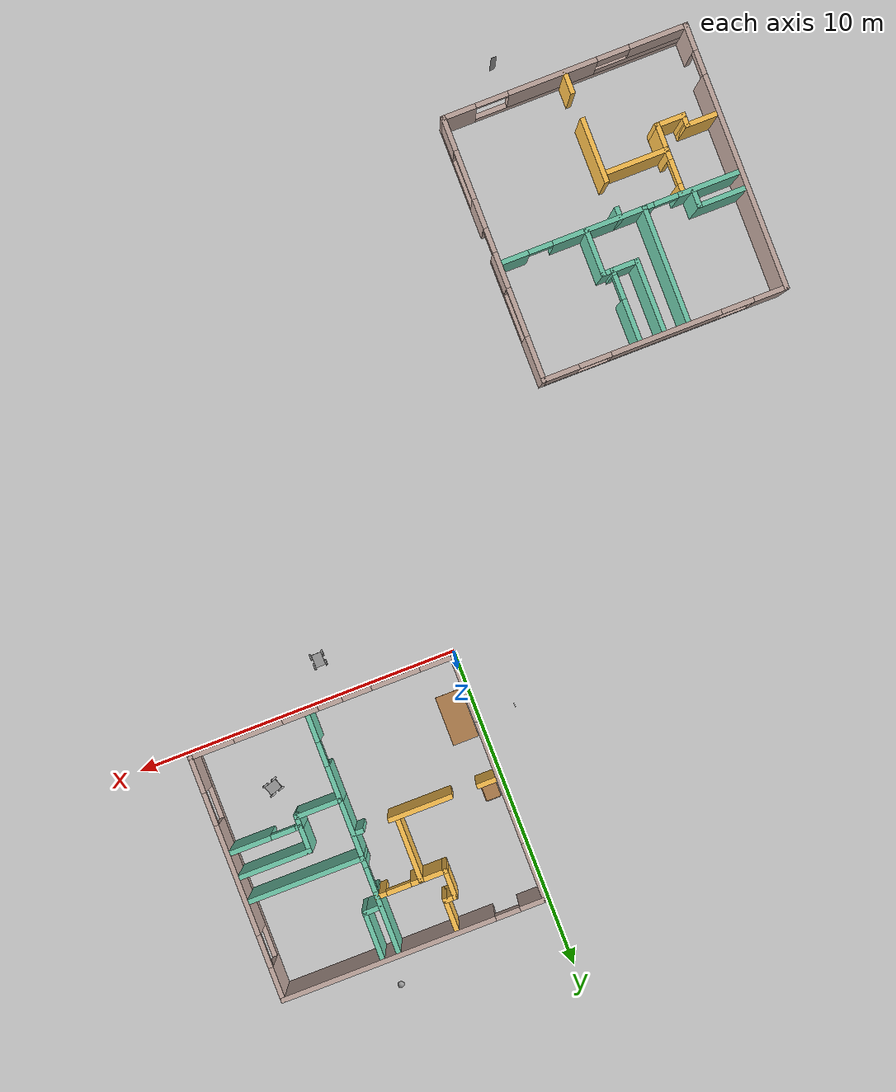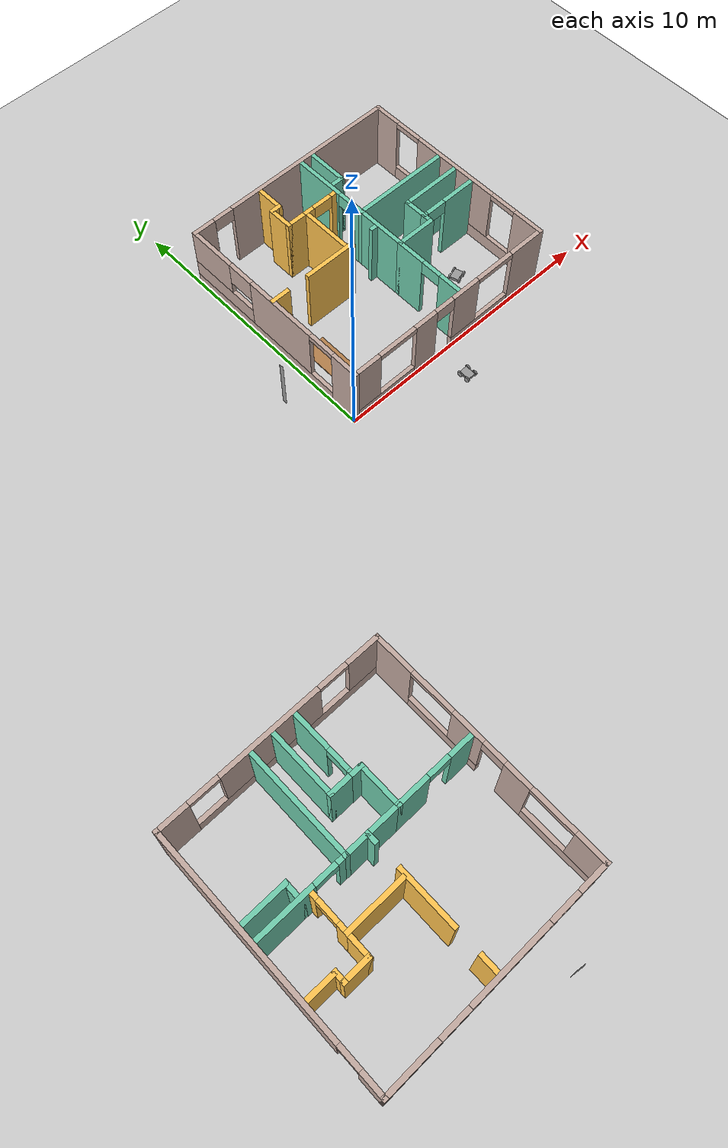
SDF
<sdf version="1.6">
 <world name="default">
  <plugin name="hello" filename="libhello.so"/>
  <light name="sun" type="directional">
   <pose>0 0 10 0 -0 0</pose>
   <diffuse>0.8 0.8 0.8 1</diffuse>
   <specular>0.2 0.2 0.2 1</specular>
   <attenuation>
    <range>1000</range>
    <constant>0.9</constant>
    <linear>0.01</linear>
    <quadratic>0.001</quadratic>
   </attenuation>
   <direction>-0.5 0.1 -0.9</direction>
   <spot><inner_angle>0</inner_angle><outer_angle>0</outer_angle><falloff>0</falloff></spot>
  </light>
  <model name="ground_plane">
   <static>1</static>
   <link name="link">
    <collision name="collision">
     <geometry><plane><normal>0 0 1</normal><size>100 100</size></plane></geometry>
     <surface>
      <contact><collide_bitmask>65535</collide_bitmask></contact>
      <friction><ode><mu>100</mu><mu2>50</mu2></ode></friction>
     </surface>
    </collision>
    <visual name="visual">
     <cast_shadows>0</cast_shadows>
     <geometry><plane><normal>0 0 1</normal><size>100 100</size></plane></geometry>
     <material>
      <script><uri>file://media/materials/scripts/gazebo.material</uri><name>Gazebo/Grey</name></script>
     </material>
    </visual>
   </link>
  </model>
  <gravity>0 0 -9.8</gravity>
  <magnetic_field>6e-06 2.3e-05 -4.2e-05</magnetic_field>
  <atmosphere type="adiabatic"/>
  <physics name="default_physics" default="0" type="ode">
   <max_step_size>0.001</max_step_size>
   <real_time_factor>1</real_time_factor>
   <real_time_update_rate>1000</real_time_update_rate>
  </physics>
  <scene><ambient>0.4 0.4 0.4 1</ambient><background>0.7 0.7 0.7 1</background><shadows>1</shadows></scene>
  <spherical_coordinates>
   <surface_model>EARTH_WGS84</surface_model>
   <latitude_deg>0</latitude_deg>
   <longitude_deg>0</longitude_deg>
   <elevation>0</elevation>
   <heading_deg>0</heading_deg>
  </spherical_coordinates>
  <model name="apartment">
   <pose>4.14003 3.78049 0 0 -0 0</pose>
   <link name="Door_1">
    <collision name="Door_1_Collision">
     <geometry><box><size>0 0.17 2</size></box></geometry>
     <pose>0 0 1 0 -0 0</pose>
    </collision>
    <visual name="Door_1_Visual">
     <pose>0 0 1 0 -0 0</pose>
     <geometry><box><size>0 0.17 2</size></box></geometry>
     <material>
      <script><uri>file://media/materials/scripts/gazebo.material</uri><name>Gazebo/Grey</name></script>
     </material>
    </visual>
    <pose>-5.25474 -1.71616 0 0 0 -3.11558</pose>
   </link>
   <link name="Wall_0">
    <pose>-0 3.75 0 0 -0 0</pose>
    <visual name="Wall_0_Visual_0">
     <pose>-3.7 0 1.25 0 -0 0</pose>
     <geometry><box><size>0.85 0.15 2.5</size></box></geometry>
     <material>
      <script><uri>file://media/materials/scripts/gazebo.material</uri><name>Gazebo/Grey</name></script>
      <ambient>0.760784 0.662745 0.627451 1</ambient>
     </material>
     <meta><layer>0</layer></meta>
    </visual>
    <collision name="Wall_0_Collision_0">
     <geometry><box><size>0.85 0.15 2.5</size></box></geometry>
     <pose>-3.7 0 1.25 0 -0 0</pose>
    </collision>
    <visual name="Wall_0_Visual_1">
     <pose>0.8 0 1.25 0 -0 0</pose>
     <geometry><box><size>6.65 0.15 2.5</size></box></geometry>
     <material>
      <script><uri>file://media/materials/scripts/gazebo.material</uri><name>Gazebo/Grey</name></script>
      <ambient>0.760784 0.662745 0.627451 1</ambient>
     </material>
     <meta><layer>0</layer></meta>
    </visual>
    <collision name="Wall_0_Collision_1">
     <geometry><box><size>6.65 0.15 2.5</size></box></geometry>
     <pose>0.8 0 1.25 0 -0 0</pose>
    </collision>
    <visual name="Wall_0_Visual_2">
     <pose>-2.9 0 2.25 0 -0 0</pose>
     <geometry><box><size>0.75 0.15 0.5</size></box></geometry>
     <material>
      <script><uri>file://media/materials/scripts/gazebo.material</uri><name>Gazebo/Grey</name></script>
      <ambient>0.760784 0.662745 0.627451 1</ambient>
     </material>
     <meta><layer>0</layer></meta>
    </visual>
    <collision name="Wall_0_Collision_2">
     <geometry><box><size>0.75 0.15 0.5</size></box></geometry>
     <pose>-2.9 0 2.25 0 -0 0</pose>
    </collision>
   </link>
   <link name="Wall_1">
    <pose>4.05 -0 0 0 -0 -1.5708</pose>
    <visual name="Wall_1_Visual_0">
     <pose>-3.2875 0 1.25 0 -0 0</pose>
     <geometry><box><size>1.075 0.15 2.5</size></box></geometry>
     <material>
      <script><uri>file://media/materials/scripts/gazebo.material</uri><name>Gazebo/Grey</name></script>
      <ambient>0.760784 0.662745 0.627451 1</ambient>
     </material>
     <meta><layer>0</layer></meta>
    </visual>
    <collision name="Wall_1_Collision_0">
     <geometry><box><size>1.075 0.15 2.5</size></box></geometry>
     <pose>-3.2875 0 1.25 0 -0 0</pose>
    </collision>
    <visual name="Wall_1_Visual_1">
     <pose>0.5375 0 0.25 0 -0 0</pose>
     <geometry><box><size>6.575 0.15 0.5</size></box></geometry>
     <material>
      <script><uri>file://media/materials/scripts/gazebo.material</uri><name>Gazebo/Grey</name></script>
      <ambient>0.760784 0.662745 0.627451 1</ambient>
     </material>
     <meta><layer>0</layer></meta>
    </visual>
    <collision name="Wall_1_Collision_1">
     <geometry><box><size>6.575 0.15 0.5</size></box></geometry>
     <pose>0.5375 0 0.25 0 -0 0</pose>
    </collision>
    <visual name="Wall_1_Visual_2">
     <pose>-0.050682 0 1.5 0 -0 0</pose>
     <geometry><box><size>3.39864 0.15 2</size></box></geometry>
     <material>
      <script><uri>file://media/materials/scripts/gazebo.material</uri><name>Gazebo/Grey</name></script>
      <ambient>0.760784 0.662745 0.627451 1</ambient>
     </material>
     <meta><layer>0</layer></meta>
    </visual>
    <collision name="Wall_1_Collision_2">
     <geometry><box><size>3.39864 0.15 2</size></box></geometry>
     <pose>-0.050682 0 1.5 0 -0 0</pose>
    </collision>
    <visual name="Wall_1_Visual_3">
     <pose>3.23682 0 1.5 0 -0 0</pose>
     <geometry><box><size>1.17636 0.15 2</size></box></geometry>
     <material>
      <script><uri>file://media/materials/scripts/gazebo.material</uri><name>Gazebo/Grey</name></script>
      <ambient>0.760784 0.662745 0.627451 1</ambient>
     </material>
     <meta><layer>0</layer></meta>
    </visual>
    <collision name="Wall_1_Collision_3">
     <geometry><box><size>1.17636 0.15 2</size></box></geometry>
     <pose>3.23682 0 1.5 0 -0 0</pose>
    </collision>
    <visual name="Wall_1_Visual_4">
     <pose>-2.25 0 2.4 0 -0 0</pose>
     <geometry><box><size>1 0.15 0.2</size></box></geometry>
     <material>
      <script><uri>file://media/materials/scripts/gazebo.material</uri><name>Gazebo/Grey</name></script>
      <ambient>0.760784 0.662745 0.627451 1</ambient>
     </material>
     <meta><layer>0</layer></meta>
    </visual>
    <collision name="Wall_1_Collision_4">
     <geometry><box><size>1 0.15 0.2</size></box></geometry>
     <pose>-2.25 0 2.4 0 -0 0</pose>
    </collision>
    <visual name="Wall_1_Visual_5">
     <pose>2.14864 0 2.4 0 -0 0</pose>
     <geometry><box><size>1 0.15 0.2</size></box></geometry>
     <material>
      <script><uri>file://media/materials/scripts/gazebo.material</uri><name>Gazebo/Grey</name></script>
      <ambient>0.760784 0.662745 0.627451 1</ambient>
     </material>
     <meta><layer>0</layer></meta>
    </visual>
    <collision name="Wall_1_Collision_5">
     <geometry><box><size>1 0.15 0.2</size></box></geometry>
     <pose>2.14864 0 2.4 0 -0 0</pose>
    </collision>
   </link>
   <link name="Wall_10">
    <collision name="Wall_10_Collision">
     <geometry><box><size>0.9 0.15 2.5</size></box></geometry>
     <pose>0 0 1.25 0 -0 0</pose>
    </collision>
    <visual name="Wall_10_Visual">
     <pose>0 0 1.25 0 -0 0</pose>
     <geometry><box><size>0.9 0.15 2.5</size></box></geometry>
     <material>
      <script><uri>file://media/materials/scripts/gazebo.material</uri><name>Gazebo/Grey</name></script>
      <ambient>0.435294 0.796078 0.67451 1</ambient>
     </material>
     <meta><layer>0</layer></meta>
    </visual>
    <pose>1.8 -0.375 0 0 -0 1.5708</pose>
   </link>
   <link name="Wall_11">
    <collision name="Wall_11_Collision">
     <geometry><box><size>2.25 0.15 2.5</size></box></geometry>
     <pose>0 0 1.25 0 -0 0</pose>
    </collision>
    <visual name="Wall_11_Visual">
     <pose>0 0 1.25 0 -0 0</pose>
     <geometry><box><size>2.25 0.15 2.5</size></box></geometry>
     <material>
      <script><uri>file://media/materials/scripts/gazebo.material</uri><name>Gazebo/Grey</name></script>
      <ambient>0.435294 0.796078 0.67451 1</ambient>
     </material>
     <meta><layer>0</layer></meta>
    </visual>
    <pose>2.85 -0 0 0 -0 0</pose>
   </link>
   <link name="Wall_13">
    <collision name="Wall_13_Collision">
     <geometry><box><size>3.6 0.15 2.5</size></box></geometry>
     <pose>0 0 1.25 0 -0 0</pose>
    </collision>
    <visual name="Wall_13_Visual">
     <pose>0 0 1.25 0 -0 0</pose>
     <geometry><box><size>3.6 0.15 2.5</size></box></geometry>
     <material>
      <script><uri>file://media/materials/scripts/gazebo.material</uri><name>Gazebo/Grey</name></script>
      <ambient>0.435294 0.796078 0.67451 1</ambient>
     </material>
     <meta><layer>0</layer></meta>
    </visual>
    <pose>2.175 0.75 0 0 -0 3.14159</pose>
   </link>
   <link name="Wall_14">
    <collision name="Wall_14_Collision">
     <geometry><box><size>1.95 0.15 2.5</size></box></geometry>
     <pose>0 0 1.25 0 -0 0</pose>
    </collision>
    <visual name="Wall_14_Visual">
     <pose>0 0 1.25 0 -0 0</pose>
     <geometry><box><size>1.95 0.15 2.5</size></box></geometry>
     <material>
      <script><uri>file://media/materials/scripts/gazebo.material</uri><name>Gazebo/Grey</name></script>
      <ambient>0.435294 0.796078 0.67451 1</ambient>
     </material>
     <meta><layer>0</layer></meta>
    </visual>
    <pose>0.45 -0.15 0 0 -0 -1.5708</pose>
   </link>
   <link name="Wall_16">
    <pose>0.45 2.175 0 0 -0 1.5708</pose>
    <visual name="Wall_16_Visual_0">
     <pose>-1.31932 0 1.25 0 -0 0</pose>
     <geometry><box><size>0.361363 0.15 2.5</size></box></geometry>
     <material>
      <script><uri>file://media/materials/scripts/gazebo.material</uri><name>Gazebo/Grey</name></script>
      <ambient>0.435294 0.796078 0.67451 1</ambient>
     </material>
     <meta><layer>0</layer></meta>
    </visual>
    <collision name="Wall_16_Collision_0">
     <geometry><box><size>0.361363 0.15 2.5</size></box></geometry>
     <pose>-1.31932 0 1.25 0 -0 0</pose>
    </collision>
    <visual name="Wall_16_Visual_1">
     <pose>0.555682 0 1.25 0 -0 0</pose>
     <geometry><box><size>1.88864 0.15 2.5</size></box></geometry>
     <material>
      <script><uri>file://media/materials/scripts/gazebo.material</uri><name>Gazebo/Grey</name></script>
      <ambient>0.435294 0.796078 0.67451 1</ambient>
     </material>
     <meta><layer>0</layer></meta>
    </visual>
    <collision name="Wall_16_Collision_1">
     <geometry><box><size>1.88864 0.15 2.5</size></box></geometry>
     <pose>0.555682 0 1.25 0 -0 0</pose>
    </collision>
    <visual name="Wall_16_Visual_2">
     <pose>-0.763637 0 2.25 0 -0 0</pose>
     <geometry><box><size>0.75 0.15 0.5</size></box></geometry>
     <material>
      <script><uri>file://media/materials/scripts/gazebo.material</uri><name>Gazebo/Grey</name></script>
      <ambient>0.435294 0.796078 0.67451 1</ambient>
     </material>
     <meta><layer>0</layer></meta>
    </visual>
    <collision name="Wall_16_Collision_2">
     <geometry><box><size>0.75 0.15 0.5</size></box></geometry>
     <pose>-0.763637 0 2.25 0 -0 0</pose>
    </collision>
   </link>
   <link name="Wall_18">
    <collision name="Wall_18_Collision">
     <geometry><box><size>0.65 0.15 2.5</size></box></geometry>
     <pose>0 0 1.25 0 -0 0</pose>
    </collision>
    <visual name="Wall_18_Visual">
     <pose>0 0 1.25 0 -0 0</pose>
     <geometry><box><size>0.65 0.15 2.5</size></box></geometry>
     <material>
      <script><uri>file://media/materials/scripts/gazebo.material</uri><name>Gazebo/Grey</name></script>
      <ambient>0.435294 0.796078 0.67451 1</ambient>
     </material>
     <meta><layer>0</layer></meta>
    </visual>
    <pose>0.7 2.25 0 0 -0 0</pose>
   </link>
   <link name="Wall_19">
    <collision name="Wall_19_Collision">
     <geometry><box><size>1.5 0.15 2.5</size></box></geometry>
     <pose>0 0 1.25 0 -0 0</pose>
    </collision>
    <visual name="Wall_19_Visual">
     <pose>0 0 1.25 0 -0 0</pose>
     <geometry><box><size>1.5 0.15 2.5</size></box></geometry>
     <material>
      <script><uri>file://media/materials/scripts/gazebo.material</uri><name>Gazebo/Grey</name></script>
      <ambient>0.435294 0.796078 0.67451 1</ambient>
     </material>
     <meta><layer>0</layer></meta>
    </visual>
    <pose>0.95 2.925 0 0 -0 1.5708</pose>
   </link>
   <link name="Wall_2">
    <pose>-0 -3.75 0 0 -0 3.14159</pose>
    <visual name="Wall_2_Visual_0">
     <pose>-3.4125 0 1.25 0 -0 0</pose>
     <geometry><box><size>1.425 0.15 2.5</size></box></geometry>
     <material>
      <script><uri>file://media/materials/scripts/gazebo.material</uri><name>Gazebo/Grey</name></script>
      <ambient>0.760784 0.662745 0.627451 1</ambient>
     </material>
     <meta><layer>0</layer></meta>
    </visual>
    <collision name="Wall_2_Collision_0">
     <geometry><box><size>1.425 0.15 2.5</size></box></geometry>
     <pose>-3.4125 0 1.25 0 -0 0</pose>
    </collision>
    <visual name="Wall_2_Visual_1">
     <pose>1.1 0 1.25 0 -0 0</pose>
     <geometry><box><size>0.899991 0.15 2.5</size></box></geometry>
     <material>
      <script><uri>file://media/materials/scripts/gazebo.material</uri><name>Gazebo/Grey</name></script>
      <ambient>0.760784 0.662745 0.627451 1</ambient>
     </material>
     <meta><layer>0</layer></meta>
    </visual>
    <collision name="Wall_2_Collision_1">
     <geometry><box><size>0.899991 0.15 2.5</size></box></geometry>
     <pose>1.1 0 1.25 0 -0 0</pose>
    </collision>
    <visual name="Wall_2_Visual_2">
     <pose>-1.4 0 0.25 0 -0 0</pose>
     <geometry><box><size>2.60001 0.15 0.5</size></box></geometry>
     <material>
      <script><uri>file://media/materials/scripts/gazebo.material</uri><name>Gazebo/Grey</name></script>
      <ambient>0.760784 0.662745 0.627451 1</ambient>
     </material>
     <meta><layer>0</layer></meta>
    </visual>
    <collision name="Wall_2_Collision_2">
     <geometry><box><size>2.60001 0.15 0.5</size></box></geometry>
     <pose>-1.4 0 0.25 0 -0 0</pose>
    </collision>
    <visual name="Wall_2_Visual_3">
     <pose>2.8375 0 0.25 0 -0 0</pose>
     <geometry><box><size>2.575 0.15 0.5</size></box></geometry>
     <material>
      <script><uri>file://media/materials/scripts/gazebo.material</uri><name>Gazebo/Grey</name></script>
      <ambient>0.760784 0.662745 0.627451 1</ambient>
     </material>
     <meta><layer>0</layer></meta>
    </visual>
    <collision name="Wall_2_Collision_3">
     <geometry><box><size>2.575 0.15 0.5</size></box></geometry>
     <pose>2.8375 0 0.25 0 -0 0</pose>
    </collision>
    <visual name="Wall_2_Visual_4">
     <pose>-0.649995 0 1.5 0 -0 0</pose>
     <geometry><box><size>1.10001 0.15 2</size></box></geometry>
     <material>
      <script><uri>file://media/materials/scripts/gazebo.material</uri><name>Gazebo/Grey</name></script>
      <ambient>0.760784 0.662745 0.627451 1</ambient>
     </material>
     <meta><layer>0</layer></meta>
    </visual>
    <collision name="Wall_2_Collision_4">
     <geometry><box><size>1.10001 0.15 2</size></box></geometry>
     <pose>-0.649995 0 1.5 0 -0 0</pose>
    </collision>
    <visual name="Wall_2_Visual_5">
     <pose>-0.649995 0 1.5 0 -0 0</pose>
     <geometry><box><size>1.10001 0.15 2</size></box></geometry>
     <material>
      <script><uri>file://media/materials/scripts/gazebo.material</uri><name>Gazebo/Grey</name></script>
      <ambient>0.760784 0.662745 0.627451 1</ambient>
     </material>
     <meta><layer>0</layer></meta>
    </visual>
    <collision name="Wall_2_Collision_5">
     <geometry><box><size>1.10001 0.15 2</size></box></geometry>
     <pose>-0.649995 0 1.5 0 -0 0</pose>
    </collision>
    <visual name="Wall_2_Visual_6">
     <pose>3.5875 0 1.5 0 -0 0</pose>
     <geometry><box><size>1.075 0.15 2</size></box></geometry>
     <material>
      <script><uri>file://media/materials/scripts/gazebo.material</uri><name>Gazebo/Grey</name></script>
      <ambient>0.760784 0.662745 0.627451 1</ambient>
     </material>
     <meta><layer>0</layer></meta>
    </visual>
    <collision name="Wall_2_Collision_6">
     <geometry><box><size>1.075 0.15 2</size></box></geometry>
     <pose>3.5875 0 1.5 0 -0 0</pose>
    </collision>
    <visual name="Wall_2_Visual_7">
     <pose>0.275009 0 2.25 0 -0 0</pose>
     <geometry><box><size>0.75 0.15 0.5</size></box></geometry>
     <material>
      <script><uri>file://media/materials/scripts/gazebo.material</uri><name>Gazebo/Grey</name></script>
      <ambient>0.760784 0.662745 0.627451 1</ambient>
     </material>
     <meta><layer>0</layer></meta>
    </visual>
    <collision name="Wall_2_Collision_7">
     <geometry><box><size>0.75 0.15 0.5</size></box></geometry>
     <pose>0.275009 0 2.25 0 -0 0</pose>
    </collision>
    <visual name="Wall_2_Visual_8">
     <pose>0.275009 0 2.25 0 -0 0</pose>
     <geometry><box><size>0.75 0.15 0.5</size></box></geometry>
     <material>
      <script><uri>file://media/materials/scripts/gazebo.material</uri><name>Gazebo/Grey</name></script>
      <ambient>0.760784 0.662745 0.627451 1</ambient>
     </material>
     <meta><layer>0</layer></meta>
    </visual>
    <collision name="Wall_2_Collision_8">
     <geometry><box><size>0.75 0.15 0.5</size></box></geometry>
     <pose>0.275009 0 2.25 0 -0 0</pose>
    </collision>
    <visual name="Wall_2_Visual_9">
     <pose>-1.95 0 2.4 0 -0 0</pose>
     <geometry><box><size>1.5 0.15 0.2</size></box></geometry>
     <material>
      <script><uri>file://media/materials/scripts/gazebo.material</uri><name>Gazebo/Grey</name></script>
      <ambient>0.760784 0.662745 0.627451 1</ambient>
     </material>
     <meta><layer>0</layer></meta>
    </visual>
    <collision name="Wall_2_Collision_9">
     <geometry><box><size>1.5 0.15 0.2</size></box></geometry>
     <pose>-1.95 0 2.4 0 -0 0</pose>
    </collision>
    <visual name="Wall_2_Visual_10">
     <pose>2.3 0 2.4 0 -0 0</pose>
     <geometry><box><size>1.5 0.15 0.2</size></box></geometry>
     <material>
      <script><uri>file://media/materials/scripts/gazebo.material</uri><name>Gazebo/Grey</name></script>
      <ambient>0.760784 0.662745 0.627451 1</ambient>
     </material>
     <meta><layer>0</layer></meta>
    </visual>
    <collision name="Wall_2_Collision_10">
     <geometry><box><size>1.5 0.15 0.2</size></box></geometry>
     <pose>2.3 0 2.4 0 -0 0</pose>
    </collision>
   </link>
   <link name="Wall_25">
    <collision name="Wall_25_Collision">
     <geometry><box><size>0.9 0.15 2.5</size></box></geometry>
     <pose>0 0 1.25 0 -0 0</pose>
    </collision>
    <visual name="Wall_25_Visual">
     <pose>0 0 1.25 0 -0 0</pose>
     <geometry><box><size>0.9 0.15 2.5</size></box></geometry>
     <material>
      <script><uri>file://media/materials/scripts/gazebo.material</uri><name>Gazebo/Grey</name></script>
      <ambient>1 0.764706 0.305882 1</ambient>
     </material>
     <meta><layer>0</layer></meta>
    </visual>
    <pose>-1.275 1.95 0 0 -0 3.14159</pose>
   </link>
   <link name="Wall_26">
    <collision name="Wall_26_Collision">
     <geometry><box><size>0.95 0.15 2.5</size></box></geometry>
     <pose>0 0 1.25 0 -0 0</pose>
    </collision>
    <visual name="Wall_26_Visual">
     <pose>0 0 1.25 0 -0 0</pose>
     <geometry><box><size>0.95 0.15 2.5</size></box></geometry>
     <material>
      <script><uri>file://media/materials/scripts/gazebo.material</uri><name>Gazebo/Grey</name></script>
      <ambient>1 0.764706 0.305882 1</ambient>
     </material>
     <meta><layer>0</layer></meta>
    </visual>
    <pose>-1.65 2.35 0 0 -0 1.5708</pose>
   </link>
   <link name="Wall_27">
    <collision name="Wall_27_Collision">
     <geometry><box><size>0.45 0.15 2.5</size></box></geometry>
     <pose>0 0 1.25 0 -0 0</pose>
    </collision>
    <visual name="Wall_27_Visual">
     <pose>0 0 1.25 0 -0 0</pose>
     <geometry><box><size>0.45 0.15 2.5</size></box></geometry>
     <material>
      <script><uri>file://media/materials/scripts/gazebo.material</uri><name>Gazebo/Grey</name></script>
      <ambient>1 0.764706 0.305882 1</ambient>
     </material>
     <meta><layer>0</layer></meta>
    </visual>
    <pose>-1.5 2.75 0 0 -0 0</pose>
   </link>
   <link name="Wall_28">
    <collision name="Wall_28_Collision">
     <geometry><box><size>1 0.15 2.5</size></box></geometry>
     <pose>0 0 1.25 0 -0 0</pose>
    </collision>
    <visual name="Wall_28_Visual">
     <pose>0 0 1.25 0 -0 0</pose>
     <geometry><box><size>1 0.15 2.5</size></box></geometry>
     <material>
      <script><uri>file://media/materials/scripts/gazebo.material</uri><name>Gazebo/Grey</name></script>
      <ambient>1 0.764706 0.305882 1</ambient>
     </material>
     <meta><layer>0</layer></meta>
    </visual>
    <pose>-1.35 3.175 0 0 -0 1.5708</pose>
   </link>
   <link name="Wall_3">
    <pose>-4.05 -0 0 0 -0 1.5708</pose>
    <visual name="Wall_3_Visual_0">
     <pose>-3.2875 0 1.25 0 -0 0</pose>
     <geometry><box><size>1.075 0.15 2.5</size></box></geometry>
     <material>
      <script><uri>file://media/materials/scripts/gazebo.material</uri><name>Gazebo/Grey</name></script>
      <ambient>0.760784 0.662745 0.627451 1</ambient>
     </material>
     <meta><layer>0</layer></meta>
    </visual>
    <collision name="Wall_3_Collision_0">
     <geometry><box><size>1.075 0.15 2.5</size></box></geometry>
     <pose>-3.2875 0 1.25 0 -0 0</pose>
    </collision>
    <visual name="Wall_3_Visual_1">
     <pose>0.5375 0 0.25 0 -0 0</pose>
     <geometry><box><size>6.575 0.15 0.5</size></box></geometry>
     <material>
      <script><uri>file://media/materials/scripts/gazebo.material</uri><name>Gazebo/Grey</name></script>
      <ambient>0.760784 0.662745 0.627451 1</ambient>
     </material>
     <meta><layer>0</layer></meta>
    </visual>
    <collision name="Wall_3_Collision_1">
     <geometry><box><size>6.575 0.15 0.5</size></box></geometry>
     <pose>0.5375 0 0.25 0 -0 0</pose>
    </collision>
    <visual name="Wall_3_Visual_2">
     <pose>-0.375 0 1.5 0 -0 0</pose>
     <geometry><box><size>2.75 0.15 2</size></box></geometry>
     <material>
      <script><uri>file://media/materials/scripts/gazebo.material</uri><name>Gazebo/Grey</name></script>
      <ambient>0.760784 0.662745 0.627451 1</ambient>
     </material>
     <meta><layer>0</layer></meta>
    </visual>
    <collision name="Wall_3_Collision_2">
     <geometry><box><size>2.75 0.15 2</size></box></geometry>
     <pose>-0.375 0 1.5 0 -0 0</pose>
    </collision>
    <visual name="Wall_3_Visual_3">
     <pose>2.4125 0 0.825 0 -0 0</pose>
     <geometry><box><size>2.825 0.15 0.65</size></box></geometry>
     <material>
      <script><uri>file://media/materials/scripts/gazebo.material</uri><name>Gazebo/Grey</name></script>
      <ambient>0.760784 0.662745 0.627451 1</ambient>
     </material>
     <meta><layer>0</layer></meta>
    </visual>
    <collision name="Wall_3_Collision_3">
     <geometry><box><size>2.825 0.15 0.65</size></box></geometry>
     <pose>2.4125 0 0.825 0 -0 0</pose>
    </collision>
    <visual name="Wall_3_Visual_4">
     <pose>2.9125 0 1.825 0 -0 0</pose>
     <geometry><box><size>1.825 0.15 1.35</size></box></geometry>
     <material>
      <script><uri>file://media/materials/scripts/gazebo.material</uri><name>Gazebo/Grey</name></script>
      <ambient>0.760784 0.662745 0.627451 1</ambient>
     </material>
     <meta><layer>0</layer></meta>
    </visual>
    <collision name="Wall_3_Collision_4">
     <geometry><box><size>1.825 0.15 1.35</size></box></geometry>
     <pose>2.9125 0 1.825 0 -0 0</pose>
    </collision>
    <visual name="Wall_3_Visual_5">
     <pose>1.5 0 2.075 0 -0 0</pose>
     <geometry><box><size>1 0.15 0.85</size></box></geometry>
     <material>
      <script><uri>file://media/materials/scripts/gazebo.material</uri><name>Gazebo/Grey</name></script>
      <ambient>0.760784 0.662745 0.627451 1</ambient>
     </material>
     <meta><layer>0</layer></meta>
    </visual>
    <collision name="Wall_3_Collision_5">
     <geometry><box><size>1 0.15 0.85</size></box></geometry>
     <pose>1.5 0 2.075 0 -0 0</pose>
    </collision>
    <visual name="Wall_3_Visual_6">
     <pose>-2.25 0 2.4 0 -0 0</pose>
     <geometry><box><size>1 0.15 0.2</size></box></geometry>
     <material>
      <script><uri>file://media/materials/scripts/gazebo.material</uri><name>Gazebo/Grey</name></script>
      <ambient>0.760784 0.662745 0.627451 1</ambient>
     </material>
     <meta><layer>0</layer></meta>
    </visual>
    <collision name="Wall_3_Collision_6">
     <geometry><box><size>1 0.15 0.2</size></box></geometry>
     <pose>-2.25 0 2.4 0 -0 0</pose>
    </collision>
   </link>
   <link name="Wall_33">
    <collision name="Wall_33_Collision">
     <geometry><box><size>2 0.15 2.5</size></box></geometry>
     <pose>0 0 1.25 0 -0 0</pose>
    </collision>
    <visual name="Wall_33_Visual">
     <pose>0 0 1.25 0 -0 0</pose>
     <geometry><box><size>2 0.15 2.5</size></box></geometry>
     <material>
      <script><uri>file://media/materials/scripts/gazebo.material</uri><name>Gazebo/Grey</name></script>
      <ambient>1 0.764706 0.305882 1</ambient>
     </material>
     <meta><layer>0</layer></meta>
    </visual>
    <pose>-1.625 -0 0 0 -0 3.14159</pose>
   </link>
   <link name="Wall_35">
    <collision name="Wall_35_Collision">
     <geometry><box><size>0.735 0.15 2.5</size></box></geometry>
     <pose>0 0 1.25 0 -0 0</pose>
    </collision>
    <visual name="Wall_35_Visual">
     <pose>0 0 1.25 0 -0 0</pose>
     <geometry><box><size>0.735 0.15 2.5</size></box></geometry>
     <material>
      <script><uri>file://media/materials/scripts/gazebo.material</uri><name>Gazebo/Grey</name></script>
      <ambient>1 0.764706 0.305882 1</ambient>
     </material>
     <meta><layer>0</layer></meta>
    </visual>
    <pose>-3.7425 -0 0 0 -0 0</pose>
   </link>
   <link name="Wall_38">
    <collision name="Wall_38_Collision">
     <geometry><box><size>0.4 0.15 2.5</size></box></geometry>
     <pose>0 0 1.25 0 -0 0</pose>
    </collision>
    <visual name="Wall_38_Visual">
     <pose>0 0 1.25 0 -0 0</pose>
     <geometry><box><size>0.4 0.15 2.5</size></box></geometry>
     <material>
      <script><uri>file://media/materials/scripts/gazebo.material</uri><name>Gazebo/Grey</name></script>
      <ambient>0.435294 0.796078 0.67451 1</ambient>
     </material>
     <meta><layer>0</layer></meta>
    </visual>
    <pose>0.325 -0 0 0 -0 3.14159</pose>
   </link>
   <link name="Wall_40">
    <collision name="Wall_40_Collision">
     <geometry><box><size>2 0.15 2.5</size></box></geometry>
     <pose>0 0 1.25 0 -0 0</pose>
    </collision>
    <visual name="Wall_40_Visual">
     <pose>0 0 1.25 0 -0 0</pose>
     <geometry><box><size>2 0.15 2.5</size></box></geometry>
     <material>
      <script><uri>file://media/materials/scripts/gazebo.material</uri><name>Gazebo/Grey</name></script>
      <ambient>1 0.764706 0.305882 1</ambient>
     </material>
     <meta><layer>0</layer></meta>
    </visual>
    <pose>-0.9 1.025 0 0 -0 -1.5708</pose>
   </link>
   <link name="Wall_42">
    <pose>-0.225 1.95 0 0 -0 0</pose>
    <visual name="Wall_42_Visual_0">
     <pose>-0.557505 0 1.25 0 -0 0</pose>
     <geometry><box><size>0.384991 0.15 2.5</size></box></geometry>
     <material>
      <script><uri>file://media/materials/scripts/gazebo.material</uri><name>Gazebo/Grey</name></script>
      <ambient>1 0.764706 0.305882 1</ambient>
     </material>
     <meta><layer>0</layer></meta>
    </visual>
    <collision name="Wall_42_Collision_0">
     <geometry><box><size>0.384991 0.15 2.5</size></box></geometry>
     <pose>-0.557505 0 1.25 0 -0 0</pose>
    </collision>
    <visual name="Wall_42_Visual_1">
     <pose>0.567495 0 1.25 0 -0 0</pose>
     <geometry><box><size>0.365009 0.15 2.5</size></box></geometry>
     <material>
      <script><uri>file://media/materials/scripts/gazebo.material</uri><name>Gazebo/Grey</name></script>
      <ambient>1 0.764706 0.305882 1</ambient>
     </material>
     <meta><layer>0</layer></meta>
    </visual>
    <collision name="Wall_42_Collision_1">
     <geometry><box><size>0.365009 0.15 2.5</size></box></geometry>
     <pose>0.567495 0 1.25 0 -0 0</pose>
    </collision>
    <visual name="Wall_42_Visual_2">
     <pose>0.009991 0 2.25 0 -0 0</pose>
     <geometry><box><size>0.75 0.15 0.5</size></box></geometry>
     <material>
      <script><uri>file://media/materials/scripts/gazebo.material</uri><name>Gazebo/Grey</name></script>
      <ambient>1 0.764706 0.305882 1</ambient>
     </material>
     <meta><layer>0</layer></meta>
    </visual>
    <collision name="Wall_42_Collision_2">
     <geometry><box><size>0.75 0.15 0.5</size></box></geometry>
     <pose>0.009991 0 2.25 0 -0 0</pose>
    </collision>
   </link>
   <link name="Wall_5">
    <pose>0.45 -2.325 0 0 -0 1.5708</pose>
    <visual name="Wall_5_Visual_0">
     <pose>-0.934318 0 1.25 0 -0 0</pose>
     <geometry><box><size>0.831364 0.15 2.5</size></box></geometry>
     <material>
      <script><uri>file://media/materials/scripts/gazebo.material</uri><name>Gazebo/Grey</name></script>
      <ambient>0.435294 0.796078 0.67451 1</ambient>
     </material>
     <meta><layer>0</layer></meta>
    </visual>
    <collision name="Wall_5_Collision_0">
     <geometry><box><size>0.831364 0.15 2.5</size></box></geometry>
     <pose>-0.934318 0 1.25 0 -0 0</pose>
    </collision>
    <visual name="Wall_5_Visual_1">
     <pose>0.790682 0 1.25 0 -0 0</pose>
     <geometry><box><size>1.11864 0.15 2.5</size></box></geometry>
     <material>
      <script><uri>file://media/materials/scripts/gazebo.material</uri><name>Gazebo/Grey</name></script>
      <ambient>0.435294 0.796078 0.67451 1</ambient>
     </material>
     <meta><layer>0</layer></meta>
    </visual>
    <collision name="Wall_5_Collision_1">
     <geometry><box><size>1.11864 0.15 2.5</size></box></geometry>
     <pose>0.790682 0 1.25 0 -0 0</pose>
    </collision>
    <visual name="Wall_5_Visual_2">
     <pose>-0.143636 0 2.25 0 -0 0</pose>
     <geometry><box><size>0.75 0.15 0.5</size></box></geometry>
     <material>
      <script><uri>file://media/materials/scripts/gazebo.material</uri><name>Gazebo/Grey</name></script>
      <ambient>0.435294 0.796078 0.67451 1</ambient>
     </material>
     <meta><layer>0</layer></meta>
    </visual>
    <collision name="Wall_5_Collision_2">
     <geometry><box><size>0.75 0.15 0.5</size></box></geometry>
     <pose>-0.143636 0 2.25 0 -0 0</pose>
    </collision>
   </link>
   <link name="Wall_6">
    <collision name="Wall_6_Collision">
     <geometry><box><size>1.5 0.15 2.5</size></box></geometry>
     <pose>0 0 1.25 0 -0 0</pose>
    </collision>
    <visual name="Wall_6_Visual">
     <pose>0 0 1.25 0 -0 0</pose>
     <geometry><box><size>1.5 0.15 2.5</size></box></geometry>
     <material>
      <script><uri>file://media/materials/scripts/gazebo.material</uri><name>Gazebo/Grey</name></script>
      <ambient>0.435294 0.796078 0.67451 1</ambient>
     </material>
     <meta><layer>0</layer></meta>
    </visual>
    <pose>1.125 -1.05 0 0 -0 0</pose>
   </link>
   <link name="Wall_7">
    <collision name="Wall_7_Collision">
     <geometry><box><size>0.45 0.15 2.5</size></box></geometry>
     <pose>0 0 1.25 0 -0 0</pose>
    </collision>
    <visual name="Wall_7_Visual">
     <pose>0 0 1.25 0 -0 0</pose>
     <geometry><box><size>0.45 0.15 2.5</size></box></geometry>
     <material>
      <script><uri>file://media/materials/scripts/gazebo.material</uri><name>Gazebo/Grey</name></script>
      <ambient>0.435294 0.796078 0.67451 1</ambient>
     </material>
     <meta><layer>0</layer></meta>
    </visual>
    <pose>1.8 -0.9 0 0 -0 1.5708</pose>
   </link>
   <link name="Wall_8">
    <pose>2.85 -0.75 0 0 -0 0</pose>
    <visual name="Wall_8_Visual_0">
     <pose>-1.01319 0 1.25 0 -0 0</pose>
     <geometry><box><size>0.223613 0.15 2.5</size></box></geometry>
     <material>
      <script><uri>file://media/materials/scripts/gazebo.material</uri><name>Gazebo/Grey</name></script>
      <ambient>0.435294 0.796078 0.67451 1</ambient>
     </material>
     <meta><layer>0</layer></meta>
    </visual>
    <collision name="Wall_8_Collision_0">
     <geometry><box><size>0.223613 0.15 2.5</size></box></geometry>
     <pose>-1.01319 0 1.25 0 -0 0</pose>
    </collision>
    <visual name="Wall_8_Visual_1">
     <pose>0.486807 0 1.25 0 -0 0</pose>
     <geometry><box><size>1.27639 0.15 2.5</size></box></geometry>
     <material>
      <script><uri>file://media/materials/scripts/gazebo.material</uri><name>Gazebo/Grey</name></script>
      <ambient>0.435294 0.796078 0.67451 1</ambient>
     </material>
     <meta><layer>0</layer></meta>
    </visual>
    <collision name="Wall_8_Collision_1">
     <geometry><box><size>1.27639 0.15 2.5</size></box></geometry>
     <pose>0.486807 0 1.25 0 -0 0</pose>
    </collision>
    <visual name="Wall_8_Visual_2">
     <pose>-0.526387 0 2.25 0 -0 0</pose>
     <geometry><box><size>0.75 0.15 0.5</size></box></geometry>
     <material>
      <script><uri>file://media/materials/scripts/gazebo.material</uri><name>Gazebo/Grey</name></script>
      <ambient>0.435294 0.796078 0.67451 1</ambient>
     </material>
     <meta><layer>0</layer></meta>
    </visual>
    <collision name="Wall_8_Collision_2">
     <geometry><box><size>0.75 0.15 0.5</size></box></geometry>
     <pose>-0.526387 0 2.25 0 -0 0</pose>
    </collision>
   </link>
   <static>1</static>
  </model>
  <model name="4wheelSmallDiff">
   <link name="link_0">
    <inertial>
     <mass>1</mass>
     <inertia>
      <ixx>0.166667</ixx>
      <ixy>0</ixy>
      <ixz>0</ixz>
      <iyy>0.166667</iyy>
      <iyz>0</iyz>
      <izz>0.166667</izz>
     </inertia>
    </inertial>
    <pose>-0.05296 -0.054413 -0.019995 0 -0 0</pose>
    <visual name="visual">
     <geometry><box><size>0.4 0.3 0.1</size></box></geometry>
     <material>
      <lighting>1</lighting>
      <script><uri>file://media/materials/scripts/gazebo.material</uri><name>Gazebo/Grey</name></script>
      <shader type="pixel"><normal_map>__default__</normal_map></shader>
      <ambient>0.3 0.3 0.3 1</ambient>
      <diffuse>0.7 0.7 0.7 1</diffuse>
      <specular>0.01 0.01 0.01 1</specular>
      <emissive>0 0 0 1</emissive>
     </material>
    </visual>
    <collision name="collision">
     <geometry><box><size>0.4 0.3 0.1</size></box></geometry>
     <surface>
      <friction>
       <ode><mu>1</mu><mu2>1</mu2><fdir1>0 0 0</fdir1><slip1>0</slip1><slip2>0</slip2></ode>
       <torsional>
        <coefficient>1</coefficient>
        <patch_radius>0</patch_radius>
        <surface_radius>0</surface_radius>
        <use_patch_radius>1</use_patch_radius>
        <ode><slip>0</slip></ode>
       </torsional>
      </friction>
      <bounce><restitution_coefficient>0</restitution_coefficient><threshold>1e+06</threshold></bounce>
      <contact>
       <collide_without_contact>0</collide_without_contact>
       <collide_without_contact_bitmask>1</collide_without_contact_bitmask>
       <collide_bitmask>1</collide_bitmask>
       <ode>
        <soft_cfm>0</soft_cfm>
        <soft_erp>0.2</soft_erp>
        <kp>1e+13</kp>
        <kd>1</kd>
        <max_vel>0.01</max_vel>
        <min_depth>0</min_depth>
       </ode>
       <bullet>
        <split_impulse>1</split_impulse>
        <split_impulse_penetration_threshold>-0.01</split_impulse_penetration_threshold>
        <soft_cfm>0</soft_cfm>
        <soft_erp>0.2</soft_erp>
        <kp>1e+13</kp>
        <kd>1</kd>
       </bullet>
      </contact>
     </surface>
    </collision>
   </link>
   <link name="link_1">
    <inertial>
     <mass>1</mass>
     <inertia><ixx>0.145833</ixx><ixy>0</ixy><ixz>0</ixz><iyy>0.145833</iyy><iyz>0</iyz><izz>0.125</izz></inertia>
    </inertial>
    <pose>-0.20296 -0.234413 -0.019995 1.5707 -0 0</pose>
    <visual name="visual">
     <geometry><cylinder><radius>0.1</radius><length>0.05</length></cylinder></geometry>
     <material>
      <lighting>1</lighting>
      <script><uri>file://media/materials/scripts/gazebo.material</uri><name>Gazebo/Grey</name></script>
      <shader type="pixel"><normal_map>__default__</normal_map></shader>
      <ambient>0.3 0.3 0.3 1</ambient>
      <diffuse>0.7 0.7 0.7 1</diffuse>
      <specular>0.01 0.01 0.01 1</specular>
      <emissive>0 0 0 1</emissive>
     </material>
    </visual>
    <collision name="collision">
     <geometry><cylinder><radius>0.1</radius><length>0.05</length></cylinder></geometry>
     <surface>
      <friction>
       <ode><mu>1</mu><mu2>1</mu2><fdir1>0 0 0</fdir1><slip1>0</slip1><slip2>0</slip2></ode>
       <torsional>
        <coefficient>1</coefficient>
        <patch_radius>0</patch_radius>
        <surface_radius>0</surface_radius>
        <use_patch_radius>1</use_patch_radius>
        <ode><slip>0</slip></ode>
       </torsional>
      </friction>
      <bounce><restitution_coefficient>0</restitution_coefficient><threshold>1e+06</threshold></bounce>
      <contact>
       <collide_without_contact>0</collide_without_contact>
       <collide_without_contact_bitmask>1</collide_without_contact_bitmask>
       <collide_bitmask>1</collide_bitmask>
       <ode>
        <soft_cfm>0</soft_cfm>
        <soft_erp>0.2</soft_erp>
        <kp>1e+13</kp>
        <kd>1</kd>
        <max_vel>0.01</max_vel>
        <min_depth>0</min_depth>
       </ode>
       <bullet>
        <split_impulse>1</split_impulse>
        <split_impulse_penetration_threshold>-0.01</split_impulse_penetration_threshold>
        <soft_cfm>0</soft_cfm>
        <soft_erp>0.2</soft_erp>
        <kp>1e+13</kp>
        <kd>1</kd>
       </bullet>
      </contact>
     </surface>
    </collision>
   </link>
   <link name="link_1_clone">
    <inertial>
     <mass>1</mass>
     <inertia><ixx>0.145833</ixx><ixy>0</ixy><ixz>0</ixz><iyy>0.145833</iyy><iyz>0</iyz><izz>0.125</izz></inertia>
    </inertial>
    <pose>0.09704 -0.234413 -0.019995 1.5707 -0 0</pose>
    <visual name="visual">
     <geometry><cylinder><radius>0.1</radius><length>0.05</length></cylinder></geometry>
     <material>
      <lighting>1</lighting>
      <script><uri>file://media/materials/scripts/gazebo.material</uri><name>Gazebo/Grey</name></script>
      <shader type="pixel"><normal_map>__default__</normal_map></shader>
      <ambient>0.3 0.3 0.3 1</ambient>
      <diffuse>0.7 0.7 0.7 1</diffuse>
      <specular>0.01 0.01 0.01 1</specular>
      <emissive>0 0 0 1</emissive>
     </material>
    </visual>
    <collision name="collision">
     <geometry><cylinder><radius>0.1</radius><length>0.05</length></cylinder></geometry>
     <surface>
      <friction>
       <ode><mu>1</mu><mu2>1</mu2><fdir1>0 0 0</fdir1><slip1>0</slip1><slip2>0</slip2></ode>
       <torsional>
        <coefficient>1</coefficient>
        <patch_radius>0</patch_radius>
        <surface_radius>0</surface_radius>
        <use_patch_radius>1</use_patch_radius>
        <ode><slip>0</slip></ode>
       </torsional>
      </friction>
      <bounce><restitution_coefficient>0</restitution_coefficient><threshold>1e+06</threshold></bounce>
      <contact>
       <collide_without_contact>0</collide_without_contact>
       <collide_without_contact_bitmask>1</collide_without_contact_bitmask>
       <collide_bitmask>1</collide_bitmask>
       <ode>
        <soft_cfm>0</soft_cfm>
        <soft_erp>0.2</soft_erp>
        <kp>1e+13</kp>
        <kd>1</kd>
        <max_vel>0.01</max_vel>
        <min_depth>0</min_depth>
       </ode>
       <bullet>
        <split_impulse>1</split_impulse>
        <split_impulse_penetration_threshold>-0.01</split_impulse_penetration_threshold>
        <soft_cfm>0</soft_cfm>
        <soft_erp>0.2</soft_erp>
        <kp>1e+13</kp>
        <kd>1</kd>
       </bullet>
      </contact>
     </surface>
    </collision>
   </link>
   <link name="link_1_clone_clone">
    <inertial>
     <mass>1</mass>
     <inertia><ixx>0.145833</ixx><ixy>0</ixy><ixz>0</ixz><iyy>0.145833</iyy><iyz>0</iyz><izz>0.125</izz></inertia>
    </inertial>
    <pose>-0.20296 0.125587 -0.019995 1.5707 -0 0</pose>
    <visual name="visual">
     <geometry><cylinder><radius>0.1</radius><length>0.05</length></cylinder></geometry>
     <material>
      <lighting>1</lighting>
      <script><uri>file://media/materials/scripts/gazebo.material</uri><name>Gazebo/Grey</name></script>
      <shader type="pixel"><normal_map>__default__</normal_map></shader>
      <ambient>0.3 0.3 0.3 1</ambient>
      <diffuse>0.7 0.7 0.7 1</diffuse>
      <specular>0.01 0.01 0.01 1</specular>
      <emissive>0 0 0 1</emissive>
     </material>
    </visual>
    <collision name="collision">
     <geometry><cylinder><radius>0.1</radius><length>0.05</length></cylinder></geometry>
     <surface>
      <friction>
       <ode><mu>1</mu><mu2>1</mu2><fdir1>0 0 0</fdir1><slip1>0</slip1><slip2>0</slip2></ode>
       <torsional>
        <coefficient>1</coefficient>
        <patch_radius>0</patch_radius>
        <surface_radius>0</surface_radius>
        <use_patch_radius>1</use_patch_radius>
        <ode><slip>0</slip></ode>
       </torsional>
      </friction>
      <bounce><restitution_coefficient>0</restitution_coefficient><threshold>1e+06</threshold></bounce>
      <contact>
       <collide_without_contact>0</collide_without_contact>
       <collide_without_contact_bitmask>1</collide_without_contact_bitmask>
       <collide_bitmask>1</collide_bitmask>
       <ode>
        <soft_cfm>0</soft_cfm>
        <soft_erp>0.2</soft_erp>
        <kp>1e+13</kp>
        <kd>1</kd>
        <max_vel>0.01</max_vel>
        <min_depth>0</min_depth>
       </ode>
       <bullet>
        <split_impulse>1</split_impulse>
        <split_impulse_penetration_threshold>-0.01</split_impulse_penetration_threshold>
        <soft_cfm>0</soft_cfm>
        <soft_erp>0.2</soft_erp>
        <kp>1e+13</kp>
        <kd>1</kd>
       </bullet>
      </contact>
     </surface>
    </collision>
   </link>
   <link name="link_1_clone_clone_clone">
    <inertial>
     <mass>1</mass>
     <inertia><ixx>0.145833</ixx><ixy>0</ixy><ixz>0</ixz><iyy>0.145833</iyy><iyz>0</iyz><izz>0.125</izz></inertia>
    </inertial>
    <pose>0.09704 0.125587 -0.019995 1.5707 -0 0</pose>
    <visual name="visual">
     <geometry><cylinder><radius>0.1</radius><length>0.05</length></cylinder></geometry>
     <material>
      <lighting>1</lighting>
      <script><uri>file://media/materials/scripts/gazebo.material</uri><name>Gazebo/Grey</name></script>
      <shader type="pixel"><normal_map>__default__</normal_map></shader>
      <ambient>0.3 0.3 0.3 1</ambient>
      <diffuse>0.7 0.7 0.7 1</diffuse>
      <specular>0.01 0.01 0.01 1</specular>
      <emissive>0 0 0 1</emissive>
     </material>
    </visual>
    <collision name="collision">
     <geometry><cylinder><radius>0.1</radius><length>0.05</length></cylinder></geometry>
     <surface>
      <friction>
       <ode><mu>1</mu><mu2>1</mu2><fdir1>0 0 0</fdir1><slip1>0</slip1><slip2>0</slip2></ode>
       <torsional>
        <coefficient>1</coefficient>
        <patch_radius>0</patch_radius>
        <surface_radius>0</surface_radius>
        <use_patch_radius>1</use_patch_radius>
        <ode><slip>0</slip></ode>
       </torsional>
      </friction>
      <bounce><restitution_coefficient>0</restitution_coefficient><threshold>1e+06</threshold></bounce>
      <contact>
       <collide_without_contact>0</collide_without_contact>
       <collide_without_contact_bitmask>1</collide_without_contact_bitmask>
       <collide_bitmask>1</collide_bitmask>
       <ode>
        <soft_cfm>0</soft_cfm>
        <soft_erp>0.2</soft_erp>
        <kp>1e+13</kp>
        <kd>1</kd>
        <max_vel>0.01</max_vel>
        <min_depth>0</min_depth>
       </ode>
       <bullet>
        <split_impulse>1</split_impulse>
        <split_impulse_penetration_threshold>-0.01</split_impulse_penetration_threshold>
        <soft_cfm>0</soft_cfm>
        <soft_erp>0.2</soft_erp>
        <kp>1e+13</kp>
        <kd>1</kd>
       </bullet>
      </contact>
     </surface>
    </collision>
   </link>
   <joint name="link_0_JOINT_0" type="revolute">
    <parent>link_0</parent>
    <child>link_1</child>
    <axis>
     <xyz>0 0 1</xyz>
     <limit>
      <lower>-1.79769e+308</lower>
      <upper>1.79769e+308</upper>
      <effort>-1</effort>
      <velocity>-1</velocity>
     </limit>
     <dynamics>
      <spring_reference>0</spring_reference>
      <spring_stiffness>0</spring_stiffness>
      <damping>0</damping>
     </dynamics>
     <use_parent_model_frame>0</use_parent_model_frame>
    </axis>
    <physics>
     <ode><limit><cfm>0</cfm><erp>0.2</erp></limit><suspension><cfm>0</cfm><erp>0.2</erp></suspension></ode>
    </physics>
   </joint>
   <joint name="link_0_JOINT_1" type="revolute">
    <parent>link_0</parent>
    <child>link_1_clone</child>
    <axis>
     <xyz>0 0 1</xyz>
     <limit>
      <lower>-1.79769e+308</lower>
      <upper>1.79769e+308</upper>
      <effort>-1</effort>
      <velocity>-1</velocity>
     </limit>
     <dynamics>
      <spring_reference>0</spring_reference>
      <spring_stiffness>0</spring_stiffness>
      <damping>0</damping>
     </dynamics>
     <use_parent_model_frame>0</use_parent_model_frame>
    </axis>
    <physics>
     <ode><limit><cfm>0</cfm><erp>0.2</erp></limit><suspension><cfm>0</cfm><erp>0.2</erp></suspension></ode>
    </physics>
   </joint>
   <joint name="link_0_JOINT_2" type="revolute">
    <parent>link_0</parent>
    <child>link_1_clone_clone</child>
    <axis>
     <xyz>0 0 1</xyz>
     <limit>
      <lower>-1.79769e+308</lower>
      <upper>1.79769e+308</upper>
      <effort>-1</effort>
      <velocity>-1</velocity>
     </limit>
     <dynamics>
      <spring_reference>0</spring_reference>
      <spring_stiffness>0</spring_stiffness>
      <damping>0</damping>
     </dynamics>
     <use_parent_model_frame>0</use_parent_model_frame>
    </axis>
    <physics>
     <ode><limit><cfm>0</cfm><erp>0.2</erp></limit><suspension><cfm>0</cfm><erp>0.2</erp></suspension></ode>
    </physics>
   </joint>
   <joint name="link_0_JOINT_3" type="revolute">
    <parent>link_0</parent>
    <child>link_1_clone_clone_clone</child>
    <axis>
     <xyz>0 0 1</xyz>
     <limit>
      <lower>-1.79769e+308</lower>
      <upper>1.79769e+308</upper>
      <effort>-1</effort>
      <velocity>-1</velocity>
     </limit>
     <dynamics>
      <spring_reference>0</spring_reference>
      <spring_stiffness>0</spring_stiffness>
      <damping>0</damping>
     </dynamics>
     <use_parent_model_frame>0</use_parent_model_frame>
    </axis>
    <physics>
     <ode><limit><cfm>0</cfm><erp>0.2</erp></limit><suspension><cfm>0</cfm><erp>0.2</erp></suspension></ode>
    </physics>
   </joint>
   <static>0</static>
   <pose>3.80566 -1.15308 0.119997 0 -0 1.58948</pose>
  </model>
  <model name="4wheelSmallDiff_0">
   <link name="link_0">
    <inertial>
     <mass>1</mass>
     <inertia>
      <ixx>0.166667</ixx>
      <ixy>0</ixy>
      <ixz>0</ixz>
      <iyy>0.166667</iyy>
      <iyz>0</iyz>
      <izz>0.166667</izz>
     </inertia>
    </inertial>
    <pose>-0.05296 -0.054413 -0.019995 0 -0 0</pose>
    <visual name="visual">
     <geometry><box><size>0.4 0.3 0.1</size></box></geometry>
     <material>
      <lighting>1</lighting>
      <script><uri>file://media/materials/scripts/gazebo.material</uri><name>Gazebo/Grey</name></script>
      <shader type="pixel"><normal_map>__default__</normal_map></shader>
      <ambient>0.3 0.3 0.3 1</ambient>
      <diffuse>0.7 0.7 0.7 1</diffuse>
      <specular>0.01 0.01 0.01 1</specular>
      <emissive>0 0 0 1</emissive>
     </material>
    </visual>
    <collision name="collision">
     <geometry><box><size>0.4 0.3 0.1</size></box></geometry>
     <surface>
      <friction>
       <ode><mu>1</mu><mu2>1</mu2><fdir1>0 0 0</fdir1><slip1>0</slip1><slip2>0</slip2></ode>
       <torsional>
        <coefficient>1</coefficient>
        <patch_radius>0</patch_radius>
        <surface_radius>0</surface_radius>
        <use_patch_radius>1</use_patch_radius>
        <ode><slip>0</slip></ode>
       </torsional>
      </friction>
      <bounce><restitution_coefficient>0</restitution_coefficient><threshold>1e+06</threshold></bounce>
      <contact>
       <collide_without_contact>0</collide_without_contact>
       <collide_without_contact_bitmask>1</collide_without_contact_bitmask>
       <collide_bitmask>1</collide_bitmask>
       <ode>
        <soft_cfm>0</soft_cfm>
        <soft_erp>0.2</soft_erp>
        <kp>1e+13</kp>
        <kd>1</kd>
        <max_vel>0.01</max_vel>
        <min_depth>0</min_depth>
       </ode>
       <bullet>
        <split_impulse>1</split_impulse>
        <split_impulse_penetration_threshold>-0.01</split_impulse_penetration_threshold>
        <soft_cfm>0</soft_cfm>
        <soft_erp>0.2</soft_erp>
        <kp>1e+13</kp>
        <kd>1</kd>
       </bullet>
      </contact>
     </surface>
    </collision>
   </link>
   <link name="link_1">
    <inertial>
     <mass>1</mass>
     <inertia><ixx>0.145833</ixx><ixy>0</ixy><ixz>0</ixz><iyy>0.145833</iyy><iyz>0</iyz><izz>0.125</izz></inertia>
    </inertial>
    <pose>-0.20296 -0.234413 -0.019995 1.5707 -0 0</pose>
    <visual name="visual">
     <geometry><cylinder><radius>0.1</radius><length>0.05</length></cylinder></geometry>
     <material>
      <lighting>1</lighting>
      <script><uri>file://media/materials/scripts/gazebo.material</uri><name>Gazebo/Grey</name></script>
      <shader type="pixel"><normal_map>__default__</normal_map></shader>
      <ambient>0.3 0.3 0.3 1</ambient>
      <diffuse>0.7 0.7 0.7 1</diffuse>
      <specular>0.01 0.01 0.01 1</specular>
      <emissive>0 0 0 1</emissive>
     </material>
    </visual>
    <collision name="collision">
     <geometry><cylinder><radius>0.1</radius><length>0.05</length></cylinder></geometry>
     <surface>
      <friction>
       <ode><mu>1</mu><mu2>1</mu2><fdir1>0 0 0</fdir1><slip1>0</slip1><slip2>0</slip2></ode>
       <torsional>
        <coefficient>1</coefficient>
        <patch_radius>0</patch_radius>
        <surface_radius>0</surface_radius>
        <use_patch_radius>1</use_patch_radius>
        <ode><slip>0</slip></ode>
       </torsional>
      </friction>
      <bounce><restitution_coefficient>0</restitution_coefficient><threshold>1e+06</threshold></bounce>
      <contact>
       <collide_without_contact>0</collide_without_contact>
       <collide_without_contact_bitmask>1</collide_without_contact_bitmask>
       <collide_bitmask>1</collide_bitmask>
       <ode>
        <soft_cfm>0</soft_cfm>
        <soft_erp>0.2</soft_erp>
        <kp>1e+13</kp>
        <kd>1</kd>
        <max_vel>0.01</max_vel>
        <min_depth>0</min_depth>
       </ode>
       <bullet>
        <split_impulse>1</split_impulse>
        <split_impulse_penetration_threshold>-0.01</split_impulse_penetration_threshold>
        <soft_cfm>0</soft_cfm>
        <soft_erp>0.2</soft_erp>
        <kp>1e+13</kp>
        <kd>1</kd>
       </bullet>
      </contact>
     </surface>
    </collision>
   </link>
   <link name="link_1_clone">
    <inertial>
     <mass>1</mass>
     <inertia><ixx>0.145833</ixx><ixy>0</ixy><ixz>0</ixz><iyy>0.145833</iyy><iyz>0</iyz><izz>0.125</izz></inertia>
    </inertial>
    <pose>0.09704 -0.234413 -0.019995 1.5707 -0 0</pose>
    <visual name="visual">
     <geometry><cylinder><radius>0.1</radius><length>0.05</length></cylinder></geometry>
     <material>
      <lighting>1</lighting>
      <script><uri>file://media/materials/scripts/gazebo.material</uri><name>Gazebo/Grey</name></script>
      <shader type="pixel"><normal_map>__default__</normal_map></shader>
      <ambient>0.3 0.3 0.3 1</ambient>
      <diffuse>0.7 0.7 0.7 1</diffuse>
      <specular>0.01 0.01 0.01 1</specular>
      <emissive>0 0 0 1</emissive>
     </material>
    </visual>
    <collision name="collision">
     <geometry><cylinder><radius>0.1</radius><length>0.05</length></cylinder></geometry>
     <surface>
      <friction>
       <ode><mu>1</mu><mu2>1</mu2><fdir1>0 0 0</fdir1><slip1>0</slip1><slip2>0</slip2></ode>
       <torsional>
        <coefficient>1</coefficient>
        <patch_radius>0</patch_radius>
        <surface_radius>0</surface_radius>
        <use_patch_radius>1</use_patch_radius>
        <ode><slip>0</slip></ode>
       </torsional>
      </friction>
      <bounce><restitution_coefficient>0</restitution_coefficient><threshold>1e+06</threshold></bounce>
      <contact>
       <collide_without_contact>0</collide_without_contact>
       <collide_without_contact_bitmask>1</collide_without_contact_bitmask>
       <collide_bitmask>1</collide_bitmask>
       <ode>
        <soft_cfm>0</soft_cfm>
        <soft_erp>0.2</soft_erp>
        <kp>1e+13</kp>
        <kd>1</kd>
        <max_vel>0.01</max_vel>
        <min_depth>0</min_depth>
       </ode>
       <bullet>
        <split_impulse>1</split_impulse>
        <split_impulse_penetration_threshold>-0.01</split_impulse_penetration_threshold>
        <soft_cfm>0</soft_cfm>
        <soft_erp>0.2</soft_erp>
        <kp>1e+13</kp>
        <kd>1</kd>
       </bullet>
      </contact>
     </surface>
    </collision>
   </link>
   <link name="link_1_clone_clone">
    <inertial>
     <mass>1</mass>
     <inertia><ixx>0.145833</ixx><ixy>0</ixy><ixz>0</ixz><iyy>0.145833</iyy><iyz>0</iyz><izz>0.125</izz></inertia>
    </inertial>
    <pose>-0.20296 0.125587 -0.019995 1.5707 -0 0</pose>
    <visual name="visual">
     <geometry><cylinder><radius>0.1</radius><length>0.05</length></cylinder></geometry>
     <material>
      <lighting>1</lighting>
      <script><uri>file://media/materials/scripts/gazebo.material</uri><name>Gazebo/Grey</name></script>
      <shader type="pixel"><normal_map>__default__</normal_map></shader>
      <ambient>0.3 0.3 0.3 1</ambient>
      <diffuse>0.7 0.7 0.7 1</diffuse>
      <specular>0.01 0.01 0.01 1</specular>
      <emissive>0 0 0 1</emissive>
     </material>
    </visual>
    <collision name="collision">
     <geometry><cylinder><radius>0.1</radius><length>0.05</length></cylinder></geometry>
     <surface>
      <friction>
       <ode><mu>1</mu><mu2>1</mu2><fdir1>0 0 0</fdir1><slip1>0</slip1><slip2>0</slip2></ode>
       <torsional>
        <coefficient>1</coefficient>
        <patch_radius>0</patch_radius>
        <surface_radius>0</surface_radius>
        <use_patch_radius>1</use_patch_radius>
        <ode><slip>0</slip></ode>
       </torsional>
      </friction>
      <bounce><restitution_coefficient>0</restitution_coefficient><threshold>1e+06</threshold></bounce>
      <contact>
       <collide_without_contact>0</collide_without_contact>
       <collide_without_contact_bitmask>1</collide_without_contact_bitmask>
       <collide_bitmask>1</collide_bitmask>
       <ode>
        <soft_cfm>0</soft_cfm>
        <soft_erp>0.2</soft_erp>
        <kp>1e+13</kp>
        <kd>1</kd>
        <max_vel>0.01</max_vel>
        <min_depth>0</min_depth>
       </ode>
       <bullet>
        <split_impulse>1</split_impulse>
        <split_impulse_penetration_threshold>-0.01</split_impulse_penetration_threshold>
        <soft_cfm>0</soft_cfm>
        <soft_erp>0.2</soft_erp>
        <kp>1e+13</kp>
        <kd>1</kd>
       </bullet>
      </contact>
     </surface>
    </collision>
   </link>
   <link name="link_1_clone_clone_clone">
    <inertial>
     <mass>1</mass>
     <inertia><ixx>0.145833</ixx><ixy>0</ixy><ixz>0</ixz><iyy>0.145833</iyy><iyz>0</iyz><izz>0.125</izz></inertia>
    </inertial>
    <pose>0.09704 0.125587 -0.019995 1.5707 -0 0</pose>
    <visual name="visual">
     <geometry><cylinder><radius>0.1</radius><length>0.05</length></cylinder></geometry>
     <material>
      <lighting>1</lighting>
      <script><uri>file://media/materials/scripts/gazebo.material</uri><name>Gazebo/Grey</name></script>
      <shader type="pixel"><normal_map>__default__</normal_map></shader>
      <ambient>0.3 0.3 0.3 1</ambient>
      <diffuse>0.7 0.7 0.7 1</diffuse>
      <specular>0.01 0.01 0.01 1</specular>
      <emissive>0 0 0 1</emissive>
     </material>
    </visual>
    <collision name="collision">
     <geometry><cylinder><radius>0.1</radius><length>0.05</length></cylinder></geometry>
     <surface>
      <friction>
       <ode><mu>1</mu><mu2>1</mu2><fdir1>0 0 0</fdir1><slip1>0</slip1><slip2>0</slip2></ode>
       <torsional>
        <coefficient>1</coefficient>
        <patch_radius>0</patch_radius>
        <surface_radius>0</surface_radius>
        <use_patch_radius>1</use_patch_radius>
        <ode><slip>0</slip></ode>
       </torsional>
      </friction>
      <bounce><restitution_coefficient>0</restitution_coefficient><threshold>1e+06</threshold></bounce>
      <contact>
       <collide_without_contact>0</collide_without_contact>
       <collide_without_contact_bitmask>1</collide_without_contact_bitmask>
       <collide_bitmask>1</collide_bitmask>
       <ode>
        <soft_cfm>0</soft_cfm>
        <soft_erp>0.2</soft_erp>
        <kp>1e+13</kp>
        <kd>1</kd>
        <max_vel>0.01</max_vel>
        <min_depth>0</min_depth>
       </ode>
       <bullet>
        <split_impulse>1</split_impulse>
        <split_impulse_penetration_threshold>-0.01</split_impulse_penetration_threshold>
        <soft_cfm>0</soft_cfm>
        <soft_erp>0.2</soft_erp>
        <kp>1e+13</kp>
        <kd>1</kd>
       </bullet>
      </contact>
     </surface>
    </collision>
   </link>
   <joint name="link_0_JOINT_0" type="revolute">
    <parent>link_0</parent>
    <child>link_1</child>
    <axis>
     <xyz>0 0 1</xyz>
     <limit>
      <lower>-1.79769e+308</lower>
      <upper>1.79769e+308</upper>
      <effort>-1</effort>
      <velocity>-1</velocity>
     </limit>
     <dynamics>
      <spring_reference>0</spring_reference>
      <spring_stiffness>0</spring_stiffness>
      <damping>0</damping>
     </dynamics>
     <use_parent_model_frame>0</use_parent_model_frame>
    </axis>
    <physics>
     <ode><limit><cfm>0</cfm><erp>0.2</erp></limit><suspension><cfm>0</cfm><erp>0.2</erp></suspension></ode>
    </physics>
   </joint>
   <joint name="link_0_JOINT_1" type="revolute">
    <parent>link_0</parent>
    <child>link_1_clone</child>
    <axis>
     <xyz>0 0 1</xyz>
     <limit>
      <lower>-1.79769e+308</lower>
      <upper>1.79769e+308</upper>
      <effort>-1</effort>
      <velocity>-1</velocity>
     </limit>
     <dynamics>
      <spring_reference>0</spring_reference>
      <spring_stiffness>0</spring_stiffness>
      <damping>0</damping>
     </dynamics>
     <use_parent_model_frame>0</use_parent_model_frame>
    </axis>
    <physics>
     <ode><limit><cfm>0</cfm><erp>0.2</erp></limit><suspension><cfm>0</cfm><erp>0.2</erp></suspension></ode>
    </physics>
   </joint>
   <joint name="link_0_JOINT_2" type="revolute">
    <parent>link_0</parent>
    <child>link_1_clone_clone</child>
    <axis>
     <xyz>0 0 1</xyz>
     <limit>
      <lower>-1.79769e+308</lower>
      <upper>1.79769e+308</upper>
      <effort>-1</effort>
      <velocity>-1</velocity>
     </limit>
     <dynamics>
      <spring_reference>0</spring_reference>
      <spring_stiffness>0</spring_stiffness>
      <damping>0</damping>
     </dynamics>
     <use_parent_model_frame>0</use_parent_model_frame>
    </axis>
    <physics>
     <ode><limit><cfm>0</cfm><erp>0.2</erp></limit><suspension><cfm>0</cfm><erp>0.2</erp></suspension></ode>
    </physics>
   </joint>
   <joint name="link_0_JOINT_3" type="revolute">
    <parent>link_0</parent>
    <child>link_1_clone_clone_clone</child>
    <axis>
     <xyz>0 0 1</xyz>
     <limit>
      <lower>-1.79769e+308</lower>
      <upper>1.79769e+308</upper>
      <effort>-1</effort>
      <velocity>-1</velocity>
     </limit>
     <dynamics>
      <spring_reference>0</spring_reference>
      <spring_stiffness>0</spring_stiffness>
      <damping>0</damping>
     </dynamics>
     <use_parent_model_frame>0</use_parent_model_frame>
    </axis>
    <physics>
     <ode><limit><cfm>0</cfm><erp>0.2</erp></limit><suspension><cfm>0</cfm><erp>0.2</erp></suspension></ode>
    </physics>
   </joint>
   <static>0</static>
   <pose>6.44165 1.7889 0.119998 4e-06 -0 -2.82522</pose>
  </model>
  <model name="table">
   <static>1</static>
   <link name="link">
    <collision name="surface">
     <pose>0 0 1 0 -0 0</pose>
     <geometry><box><size>1.5 0.8 0.03</size></box></geometry>
     <surface><friction><ode><mu>0.6</mu><mu2>0.6</mu2></ode></friction></surface>
    </collision>
    <visual name="visual1">
     <pose>0 0 1 0 -0 0</pose>
     <geometry><box><size>1.5 0.8 0.03</size></box></geometry>
     <material>
      <script><uri>file://media/materials/scripts/gazebo.material</uri><name>Gazebo/Wood</name></script>
     </material>
    </visual>
    <collision name="front_left_leg">
     <pose>0.68 0.38 0.5 0 -0 0</pose>
     <geometry><cylinder><radius>0.02</radius><length>1</length></cylinder></geometry>
    </collision>
    <visual name="front_left_leg">
     <pose>0.68 0.38 0.5 0 -0 0</pose>
     <geometry><cylinder><radius>0.02</radius><length>1</length></cylinder></geometry>
     <material>
      <script><uri>file://media/materials/scripts/gazebo.material</uri><name>Gazebo/Grey</name></script>
     </material>
    </visual>
    <collision name="front_right_leg">
     <pose>0.68 -0.38 0.5 0 -0 0</pose>
     <geometry><cylinder><radius>0.02</radius><length>1</length></cylinder></geometry>
    </collision>
    <visual name="front_right_leg">
     <pose>0.68 -0.38 0.5 0 -0 0</pose>
     <geometry><cylinder><radius>0.02</radius><length>1</length></cylinder></geometry>
     <material>
      <script><uri>file://media/materials/scripts/gazebo.material</uri><name>Gazebo/Grey</name></script>
     </material>
    </visual>
    <collision name="back_right_leg">
     <pose>-0.68 -0.38 0.5 0 -0 0</pose>
     <geometry><cylinder><radius>0.02</radius><length>1</length></cylinder></geometry>
    </collision>
    <visual name="back_right_leg">
     <pose>-0.68 -0.38 0.5 0 -0 0</pose>
     <geometry><cylinder><radius>0.02</radius><length>1</length></cylinder></geometry>
     <material>
      <script><uri>file://media/materials/scripts/gazebo.material</uri><name>Gazebo/Grey</name></script>
     </material>
    </visual>
    <collision name="back_left_leg">
     <pose>-0.68 0.38 0.5 0 -0 0</pose>
     <geometry><cylinder><radius>0.02</radius><length>1</length></cylinder></geometry>
    </collision>
    <visual name="back_left_leg">
     <pose>-0.68 0.38 0.5 0 -0 0</pose>
     <geometry><cylinder><radius>0.02</radius><length>1</length></cylinder></geometry>
     <material>
      <script><uri>file://media/materials/scripts/gazebo.material</uri><name>Gazebo/Grey</name></script>
     </material>
    </visual>
   </link>
   <pose>0.6 1.8 0 0 -0 1.5707</pose>
  </model>
  <model name="cabinet">
   <static>1</static>
   <link name="cabinet_bottom_plate">
    <inertial>
     <pose>0 0 -1 0 -0 0</pose>
     <inertia><ixx>2.05</ixx><ixy>0</ixy><ixz>0</ixz><iyy>2.05</iyy><iyz>0</iyz><izz>2.05</izz></inertia>
     <mass>25</mass>
    </inertial>
    <collision name="cabinet_bottom_plate_geom">
     <pose>0 0 0.01 0 -0 0</pose>
     <geometry><box><size>0.45 0.45 0.02</size></box></geometry>
    </collision>
    <visual name="cabinet_bottom_plate_geom_visual">
     <pose>0 0 0.01 0 -0 0</pose>
     <geometry><box><size>0.45 0.45 0.02</size></box></geometry>
     <material>
      <script><uri>file://media/materials/scripts/gazebo.material</uri><name>Gazebo/Wood</name></script>
     </material>
    </visual>
    <collision name="cabinet_bottom_plate_geom_cabinet_back_plate">
     <pose>0.235 0 0.51 0 -0 0</pose>
     <geometry><box><size>0.02 0.45 1.02</size></box></geometry>
    </collision>
    <visual name="cabinet_bottom_plate_geom_cabinet_back_plate_visual">
     <pose>0.235 0 0.51 0 -0 0</pose>
     <geometry><box><size>0.02 0.45 1.02</size></box></geometry>
     <material>
      <script><uri>file://media/materials/scripts/gazebo.material</uri><name>Gazebo/Wood</name></script>
     </material>
    </visual>
    <collision name="cabinet_bottom_plate_geom_cabinet_left_plate">
     <pose>0 0.235 0.51 0 -0 0</pose>
     <geometry><box><size>0.45 0.02 1.02</size></box></geometry>
    </collision>
    <visual name="cabinet_bottom_plate_geom_cabinet_left_plate_visual">
     <pose>0 0.235 0.51 0 -0 0</pose>
     <geometry><box><size>0.45 0.02 1.02</size></box></geometry>
     <material>
      <script><uri>file://media/materials/scripts/gazebo.material</uri><name>Gazebo/Wood</name></script>
     </material>
    </visual>
    <collision name="cabinet_bottom_plate_geom_cabinet_middle_plate">
     <pose>0 0 0.51 0 -0 0</pose>
     <geometry><box><size>0.45 0.45 0.02</size></box></geometry>
    </collision>
    <visual name="cabinet_bottom_plate_geom_cabinet_middle_plate_visual">
     <pose>0 0 0.51 0 -0 0</pose>
     <geometry><box><size>0.45 0.45 0.02</size></box></geometry>
     <material>
      <script><uri>file://media/materials/scripts/gazebo.material</uri><name>Gazebo/Wood</name></script>
     </material>
    </visual>
    <collision name="cabinet_bottom_plate_geom_cabinet_right_plate">
     <pose>0 -0.235 0.51 0 -0 0</pose>
     <geometry><box><size>0.45 0.02 1.02</size></box></geometry>
    </collision>
    <visual name="cabinet_bottom_plate_geom_cabinet_right_plate_visual">
     <pose>0 -0.235 0.51 0 -0 0</pose>
     <geometry><box><size>0.45 0.02 1.02</size></box></geometry>
     <material>
      <script><uri>file://media/materials/scripts/gazebo.material</uri><name>Gazebo/Wood</name></script>
     </material>
    </visual>
    <collision name="cabinet_bottom_plate_geom_cabinet_top_plate">
     <pose>0 0 1.01 0 -0 0</pose>
     <geometry><box><size>0.45 0.45 0.02</size></box></geometry>
    </collision>
    <visual name="cabinet_bottom_plate_geom_cabinet_top_plate_visual">
     <pose>0 0 1.01 0 -0 0</pose>
     <geometry><box><size>0.45 0.45 0.02</size></box></geometry>
     <material>
      <script><uri>file://media/materials/scripts/gazebo.material</uri><name>Gazebo/Wood</name></script>
     </material>
    </visual>
   </link>
   <pose>0.43974 4.2 0 0 -0 0</pose>
  </model>
  <model name="apartment_0">
   <pose>-9 -10.5424 0 0 -0 1.5707</pose>
   <link name="Door_1">
    <collision name="Door_1_Collision">
     <geometry><box><size>0 0.17 2</size></box></geometry>
     <pose>0 0 1 0 -0 0</pose>
    </collision>
    <visual name="Door_1_Visual">
     <pose>0 0 1 0 -0 0</pose>
     <geometry><box><size>0 0.17 2</size></box></geometry>
     <material>
      <script><uri>file://media/materials/scripts/gazebo.material</uri><name>Gazebo/Grey</name></script>
     </material>
    </visual>
    <pose>-5.25474 -1.71616 0 0 0 -3.11558</pose>
   </link>
   <link name="Wall_0">
    <pose>-0 3.75 0 0 -0 0</pose>
    <visual name="Wall_0_Visual_0">
     <pose>-3.7 0 1.25 0 -0 0</pose>
     <geometry><box><size>0.85 0.15 2.5</size></box></geometry>
     <material>
      <script><uri>file://media/materials/scripts/gazebo.material</uri><name>Gazebo/Grey</name></script>
      <ambient>0.760784 0.662745 0.627451 1</ambient>
     </material>
     <meta><layer>0</layer></meta>
    </visual>
    <collision name="Wall_0_Collision_0">
     <geometry><box><size>0.85 0.15 2.5</size></box></geometry>
     <pose>-3.7 0 1.25 0 -0 0</pose>
    </collision>
    <visual name="Wall_0_Visual_1">
     <pose>0.8 0 1.25 0 -0 0</pose>
     <geometry><box><size>6.65 0.15 2.5</size></box></geometry>
     <material>
      <script><uri>file://media/materials/scripts/gazebo.material</uri><name>Gazebo/Grey</name></script>
      <ambient>0.760784 0.662745 0.627451 1</ambient>
     </material>
     <meta><layer>0</layer></meta>
    </visual>
    <collision name="Wall_0_Collision_1">
     <geometry><box><size>6.65 0.15 2.5</size></box></geometry>
     <pose>0.8 0 1.25 0 -0 0</pose>
    </collision>
    <visual name="Wall_0_Visual_2">
     <pose>-2.9 0 2.25 0 -0 0</pose>
     <geometry><box><size>0.75 0.15 0.5</size></box></geometry>
     <material>
      <script><uri>file://media/materials/scripts/gazebo.material</uri><name>Gazebo/Grey</name></script>
      <ambient>0.760784 0.662745 0.627451 1</ambient>
     </material>
     <meta><layer>0</layer></meta>
    </visual>
    <collision name="Wall_0_Collision_2">
     <geometry><box><size>0.75 0.15 0.5</size></box></geometry>
     <pose>-2.9 0 2.25 0 -0 0</pose>
    </collision>
   </link>
   <link name="Wall_1">
    <pose>4.05 -0 0 0 -0 -1.5708</pose>
    <visual name="Wall_1_Visual_0">
     <pose>-3.2875 0 1.25 0 -0 0</pose>
     <geometry><box><size>1.075 0.15 2.5</size></box></geometry>
     <material>
      <script><uri>file://media/materials/scripts/gazebo.material</uri><name>Gazebo/Grey</name></script>
      <ambient>0.760784 0.662745 0.627451 1</ambient>
     </material>
     <meta><layer>0</layer></meta>
    </visual>
    <collision name="Wall_1_Collision_0">
     <geometry><box><size>1.075 0.15 2.5</size></box></geometry>
     <pose>-3.2875 0 1.25 0 -0 0</pose>
    </collision>
    <visual name="Wall_1_Visual_1">
     <pose>0.5375 0 0.25 0 -0 0</pose>
     <geometry><box><size>6.575 0.15 0.5</size></box></geometry>
     <material>
      <script><uri>file://media/materials/scripts/gazebo.material</uri><name>Gazebo/Grey</name></script>
      <ambient>0.760784 0.662745 0.627451 1</ambient>
     </material>
     <meta><layer>0</layer></meta>
    </visual>
    <collision name="Wall_1_Collision_1">
     <geometry><box><size>6.575 0.15 0.5</size></box></geometry>
     <pose>0.5375 0 0.25 0 -0 0</pose>
    </collision>
    <visual name="Wall_1_Visual_2">
     <pose>-0.050682 0 1.5 0 -0 0</pose>
     <geometry><box><size>3.39864 0.15 2</size></box></geometry>
     <material>
      <script><uri>file://media/materials/scripts/gazebo.material</uri><name>Gazebo/Grey</name></script>
      <ambient>0.760784 0.662745 0.627451 1</ambient>
     </material>
     <meta><layer>0</layer></meta>
    </visual>
    <collision name="Wall_1_Collision_2">
     <geometry><box><size>3.39864 0.15 2</size></box></geometry>
     <pose>-0.050682 0 1.5 0 -0 0</pose>
    </collision>
    <visual name="Wall_1_Visual_3">
     <pose>3.23682 0 1.5 0 -0 0</pose>
     <geometry><box><size>1.17636 0.15 2</size></box></geometry>
     <material>
      <script><uri>file://media/materials/scripts/gazebo.material</uri><name>Gazebo/Grey</name></script>
      <ambient>0.760784 0.662745 0.627451 1</ambient>
     </material>
     <meta><layer>0</layer></meta>
    </visual>
    <collision name="Wall_1_Collision_3">
     <geometry><box><size>1.17636 0.15 2</size></box></geometry>
     <pose>3.23682 0 1.5 0 -0 0</pose>
    </collision>
    <visual name="Wall_1_Visual_4">
     <pose>-2.25 0 2.4 0 -0 0</pose>
     <geometry><box><size>1 0.15 0.2</size></box></geometry>
     <material>
      <script><uri>file://media/materials/scripts/gazebo.material</uri><name>Gazebo/Grey</name></script>
      <ambient>0.760784 0.662745 0.627451 1</ambient>
     </material>
     <meta><layer>0</layer></meta>
    </visual>
    <collision name="Wall_1_Collision_4">
     <geometry><box><size>1 0.15 0.2</size></box></geometry>
     <pose>-2.25 0 2.4 0 -0 0</pose>
    </collision>
    <visual name="Wall_1_Visual_5">
     <pose>2.14864 0 2.4 0 -0 0</pose>
     <geometry><box><size>1 0.15 0.2</size></box></geometry>
     <material>
      <script><uri>file://media/materials/scripts/gazebo.material</uri><name>Gazebo/Grey</name></script>
      <ambient>0.760784 0.662745 0.627451 1</ambient>
     </material>
     <meta><layer>0</layer></meta>
    </visual>
    <collision name="Wall_1_Collision_5">
     <geometry><box><size>1 0.15 0.2</size></box></geometry>
     <pose>2.14864 0 2.4 0 -0 0</pose>
    </collision>
   </link>
   <link name="Wall_10">
    <collision name="Wall_10_Collision">
     <geometry><box><size>0.9 0.15 2.5</size></box></geometry>
     <pose>0 0 1.25 0 -0 0</pose>
    </collision>
    <visual name="Wall_10_Visual">
     <pose>0 0 1.25 0 -0 0</pose>
     <geometry><box><size>0.9 0.15 2.5</size></box></geometry>
     <material>
      <script><uri>file://media/materials/scripts/gazebo.material</uri><name>Gazebo/Grey</name></script>
      <ambient>0.435294 0.796078 0.67451 1</ambient>
     </material>
     <meta><layer>0</layer></meta>
    </visual>
    <pose>1.8 -0.375 0 0 -0 1.5708</pose>
   </link>
   <link name="Wall_11">
    <collision name="Wall_11_Collision">
     <geometry><box><size>2.25 0.15 2.5</size></box></geometry>
     <pose>0 0 1.25 0 -0 0</pose>
    </collision>
    <visual name="Wall_11_Visual">
     <pose>0 0 1.25 0 -0 0</pose>
     <geometry><box><size>2.25 0.15 2.5</size></box></geometry>
     <material>
      <script><uri>file://media/materials/scripts/gazebo.material</uri><name>Gazebo/Grey</name></script>
      <ambient>0.435294 0.796078 0.67451 1</ambient>
     </material>
     <meta><layer>0</layer></meta>
    </visual>
    <pose>2.85 -0 0 0 -0 0</pose>
   </link>
   <link name="Wall_13">
    <collision name="Wall_13_Collision">
     <geometry><box><size>3.6 0.15 2.5</size></box></geometry>
     <pose>0 0 1.25 0 -0 0</pose>
    </collision>
    <visual name="Wall_13_Visual">
     <pose>0 0 1.25 0 -0 0</pose>
     <geometry><box><size>3.6 0.15 2.5</size></box></geometry>
     <material>
      <script><uri>file://media/materials/scripts/gazebo.material</uri><name>Gazebo/Grey</name></script>
      <ambient>0.435294 0.796078 0.67451 1</ambient>
     </material>
     <meta><layer>0</layer></meta>
    </visual>
    <pose>2.175 0.75 0 0 -0 3.14159</pose>
   </link>
   <link name="Wall_14">
    <collision name="Wall_14_Collision">
     <geometry><box><size>1.95 0.15 2.5</size></box></geometry>
     <pose>0 0 1.25 0 -0 0</pose>
    </collision>
    <visual name="Wall_14_Visual">
     <pose>0 0 1.25 0 -0 0</pose>
     <geometry><box><size>1.95 0.15 2.5</size></box></geometry>
     <material>
      <script><uri>file://media/materials/scripts/gazebo.material</uri><name>Gazebo/Grey</name></script>
      <ambient>0.435294 0.796078 0.67451 1</ambient>
     </material>
     <meta><layer>0</layer></meta>
    </visual>
    <pose>0.45 -0.15 0 0 -0 -1.5708</pose>
   </link>
   <link name="Wall_16">
    <pose>0.45 2.175 0 0 -0 1.5708</pose>
    <visual name="Wall_16_Visual_0">
     <pose>-1.31932 0 1.25 0 -0 0</pose>
     <geometry><box><size>0.361363 0.15 2.5</size></box></geometry>
     <material>
      <script><uri>file://media/materials/scripts/gazebo.material</uri><name>Gazebo/Grey</name></script>
      <ambient>0.435294 0.796078 0.67451 1</ambient>
     </material>
     <meta><layer>0</layer></meta>
    </visual>
    <collision name="Wall_16_Collision_0">
     <geometry><box><size>0.361363 0.15 2.5</size></box></geometry>
     <pose>-1.31932 0 1.25 0 -0 0</pose>
    </collision>
    <visual name="Wall_16_Visual_1">
     <pose>0.555682 0 1.25 0 -0 0</pose>
     <geometry><box><size>1.88864 0.15 2.5</size></box></geometry>
     <material>
      <script><uri>file://media/materials/scripts/gazebo.material</uri><name>Gazebo/Grey</name></script>
      <ambient>0.435294 0.796078 0.67451 1</ambient>
     </material>
     <meta><layer>0</layer></meta>
    </visual>
    <collision name="Wall_16_Collision_1">
     <geometry><box><size>1.88864 0.15 2.5</size></box></geometry>
     <pose>0.555682 0 1.25 0 -0 0</pose>
    </collision>
    <visual name="Wall_16_Visual_2">
     <pose>-0.763637 0 2.25 0 -0 0</pose>
     <geometry><box><size>0.75 0.15 0.5</size></box></geometry>
     <material>
      <script><uri>file://media/materials/scripts/gazebo.material</uri><name>Gazebo/Grey</name></script>
      <ambient>0.435294 0.796078 0.67451 1</ambient>
     </material>
     <meta><layer>0</layer></meta>
    </visual>
    <collision name="Wall_16_Collision_2">
     <geometry><box><size>0.75 0.15 0.5</size></box></geometry>
     <pose>-0.763637 0 2.25 0 -0 0</pose>
    </collision>
   </link>
   <link name="Wall_18">
    <collision name="Wall_18_Collision">
     <geometry><box><size>0.65 0.15 2.5</size></box></geometry>
     <pose>0 0 1.25 0 -0 0</pose>
    </collision>
    <visual name="Wall_18_Visual">
     <pose>0 0 1.25 0 -0 0</pose>
     <geometry><box><size>0.65 0.15 2.5</size></box></geometry>
     <material>
      <script><uri>file://media/materials/scripts/gazebo.material</uri><name>Gazebo/Grey</name></script>
      <ambient>0.435294 0.796078 0.67451 1</ambient>
     </material>
     <meta><layer>0</layer></meta>
    </visual>
    <pose>0.7 2.25 0 0 -0 0</pose>
   </link>
   <link name="Wall_19">
    <collision name="Wall_19_Collision">
     <geometry><box><size>1.5 0.15 2.5</size></box></geometry>
     <pose>0 0 1.25 0 -0 0</pose>
    </collision>
    <visual name="Wall_19_Visual">
     <pose>0 0 1.25 0 -0 0</pose>
     <geometry><box><size>1.5 0.15 2.5</size></box></geometry>
     <material>
      <script><uri>file://media/materials/scripts/gazebo.material</uri><name>Gazebo/Grey</name></script>
      <ambient>0.435294 0.796078 0.67451 1</ambient>
     </material>
     <meta><layer>0</layer></meta>
    </visual>
    <pose>0.95 2.925 0 0 -0 1.5708</pose>
   </link>
   <link name="Wall_2">
    <pose>-0 -3.75 0 0 -0 3.14159</pose>
    <visual name="Wall_2_Visual_0">
     <pose>-3.4125 0 1.25 0 -0 0</pose>
     <geometry><box><size>1.425 0.15 2.5</size></box></geometry>
     <material>
      <script><uri>file://media/materials/scripts/gazebo.material</uri><name>Gazebo/Grey</name></script>
      <ambient>0.760784 0.662745 0.627451 1</ambient>
     </material>
     <meta><layer>0</layer></meta>
    </visual>
    <collision name="Wall_2_Collision_0">
     <geometry><box><size>1.425 0.15 2.5</size></box></geometry>
     <pose>-3.4125 0 1.25 0 -0 0</pose>
    </collision>
    <visual name="Wall_2_Visual_1">
     <pose>1.1 0 1.25 0 -0 0</pose>
     <geometry><box><size>0.899991 0.15 2.5</size></box></geometry>
     <material>
      <script><uri>file://media/materials/scripts/gazebo.material</uri><name>Gazebo/Grey</name></script>
      <ambient>0.760784 0.662745 0.627451 1</ambient>
     </material>
     <meta><layer>0</layer></meta>
    </visual>
    <collision name="Wall_2_Collision_1">
     <geometry><box><size>0.899991 0.15 2.5</size></box></geometry>
     <pose>1.1 0 1.25 0 -0 0</pose>
    </collision>
    <visual name="Wall_2_Visual_2">
     <pose>-1.4 0 0.25 0 -0 0</pose>
     <geometry><box><size>2.60001 0.15 0.5</size></box></geometry>
     <material>
      <script><uri>file://media/materials/scripts/gazebo.material</uri><name>Gazebo/Grey</name></script>
      <ambient>0.760784 0.662745 0.627451 1</ambient>
     </material>
     <meta><layer>0</layer></meta>
    </visual>
    <collision name="Wall_2_Collision_2">
     <geometry><box><size>2.60001 0.15 0.5</size></box></geometry>
     <pose>-1.4 0 0.25 0 -0 0</pose>
    </collision>
    <visual name="Wall_2_Visual_3">
     <pose>2.8375 0 0.25 0 -0 0</pose>
     <geometry><box><size>2.575 0.15 0.5</size></box></geometry>
     <material>
      <script><uri>file://media/materials/scripts/gazebo.material</uri><name>Gazebo/Grey</name></script>
      <ambient>0.760784 0.662745 0.627451 1</ambient>
     </material>
     <meta><layer>0</layer></meta>
    </visual>
    <collision name="Wall_2_Collision_3">
     <geometry><box><size>2.575 0.15 0.5</size></box></geometry>
     <pose>2.8375 0 0.25 0 -0 0</pose>
    </collision>
    <visual name="Wall_2_Visual_4">
     <pose>-0.649995 0 1.5 0 -0 0</pose>
     <geometry><box><size>1.10001 0.15 2</size></box></geometry>
     <material>
      <script><uri>file://media/materials/scripts/gazebo.material</uri><name>Gazebo/Grey</name></script>
      <ambient>0.760784 0.662745 0.627451 1</ambient>
     </material>
     <meta><layer>0</layer></meta>
    </visual>
    <collision name="Wall_2_Collision_4">
     <geometry><box><size>1.10001 0.15 2</size></box></geometry>
     <pose>-0.649995 0 1.5 0 -0 0</pose>
    </collision>
    <visual name="Wall_2_Visual_5">
     <pose>-0.649995 0 1.5 0 -0 0</pose>
     <geometry><box><size>1.10001 0.15 2</size></box></geometry>
     <material>
      <script><uri>file://media/materials/scripts/gazebo.material</uri><name>Gazebo/Grey</name></script>
      <ambient>0.760784 0.662745 0.627451 1</ambient>
     </material>
     <meta><layer>0</layer></meta>
    </visual>
    <collision name="Wall_2_Collision_5">
     <geometry><box><size>1.10001 0.15 2</size></box></geometry>
     <pose>-0.649995 0 1.5 0 -0 0</pose>
    </collision>
    <visual name="Wall_2_Visual_6">
     <pose>3.5875 0 1.5 0 -0 0</pose>
     <geometry><box><size>1.075 0.15 2</size></box></geometry>
     <material>
      <script><uri>file://media/materials/scripts/gazebo.material</uri><name>Gazebo/Grey</name></script>
      <ambient>0.760784 0.662745 0.627451 1</ambient>
     </material>
     <meta><layer>0</layer></meta>
    </visual>
    <collision name="Wall_2_Collision_6">
     <geometry><box><size>1.075 0.15 2</size></box></geometry>
     <pose>3.5875 0 1.5 0 -0 0</pose>
    </collision>
    <visual name="Wall_2_Visual_7">
     <pose>0.275009 0 2.25 0 -0 0</pose>
     <geometry><box><size>0.75 0.15 0.5</size></box></geometry>
     <material>
      <script><uri>file://media/materials/scripts/gazebo.material</uri><name>Gazebo/Grey</name></script>
      <ambient>0.760784 0.662745 0.627451 1</ambient>
     </material>
     <meta><layer>0</layer></meta>
    </visual>
    <collision name="Wall_2_Collision_7">
     <geometry><box><size>0.75 0.15 0.5</size></box></geometry>
     <pose>0.275009 0 2.25 0 -0 0</pose>
    </collision>
    <visual name="Wall_2_Visual_8">
     <pose>0.275009 0 2.25 0 -0 0</pose>
     <geometry><box><size>0.75 0.15 0.5</size></box></geometry>
     <material>
      <script><uri>file://media/materials/scripts/gazebo.material</uri><name>Gazebo/Grey</name></script>
      <ambient>0.760784 0.662745 0.627451 1</ambient>
     </material>
     <meta><layer>0</layer></meta>
    </visual>
    <collision name="Wall_2_Collision_8">
     <geometry><box><size>0.75 0.15 0.5</size></box></geometry>
     <pose>0.275009 0 2.25 0 -0 0</pose>
    </collision>
    <visual name="Wall_2_Visual_9">
     <pose>-1.95 0 2.4 0 -0 0</pose>
     <geometry><box><size>1.5 0.15 0.2</size></box></geometry>
     <material>
      <script><uri>file://media/materials/scripts/gazebo.material</uri><name>Gazebo/Grey</name></script>
      <ambient>0.760784 0.662745 0.627451 1</ambient>
     </material>
     <meta><layer>0</layer></meta>
    </visual>
    <collision name="Wall_2_Collision_9">
     <geometry><box><size>1.5 0.15 0.2</size></box></geometry>
     <pose>-1.95 0 2.4 0 -0 0</pose>
    </collision>
    <visual name="Wall_2_Visual_10">
     <pose>2.3 0 2.4 0 -0 0</pose>
     <geometry><box><size>1.5 0.15 0.2</size></box></geometry>
     <material>
      <script><uri>file://media/materials/scripts/gazebo.material</uri><name>Gazebo/Grey</name></script>
      <ambient>0.760784 0.662745 0.627451 1</ambient>
     </material>
     <meta><layer>0</layer></meta>
    </visual>
    <collision name="Wall_2_Collision_10">
     <geometry><box><size>1.5 0.15 0.2</size></box></geometry>
     <pose>2.3 0 2.4 0 -0 0</pose>
    </collision>
   </link>
   <link name="Wall_25">
    <collision name="Wall_25_Collision">
     <geometry><box><size>0.9 0.15 2.5</size></box></geometry>
     <pose>0 0 1.25 0 -0 0</pose>
    </collision>
    <visual name="Wall_25_Visual">
     <pose>0 0 1.25 0 -0 0</pose>
     <geometry><box><size>0.9 0.15 2.5</size></box></geometry>
     <material>
      <script><uri>file://media/materials/scripts/gazebo.material</uri><name>Gazebo/Grey</name></script>
      <ambient>1 0.764706 0.305882 1</ambient>
     </material>
     <meta><layer>0</layer></meta>
    </visual>
    <pose>-1.275 1.95 0 0 -0 3.14159</pose>
   </link>
   <link name="Wall_26">
    <collision name="Wall_26_Collision">
     <geometry><box><size>0.95 0.15 2.5</size></box></geometry>
     <pose>0 0 1.25 0 -0 0</pose>
    </collision>
    <visual name="Wall_26_Visual">
     <pose>0 0 1.25 0 -0 0</pose>
     <geometry><box><size>0.95 0.15 2.5</size></box></geometry>
     <material>
      <script><uri>file://media/materials/scripts/gazebo.material</uri><name>Gazebo/Grey</name></script>
      <ambient>1 0.764706 0.305882 1</ambient>
     </material>
     <meta><layer>0</layer></meta>
    </visual>
    <pose>-1.65 2.35 0 0 -0 1.5708</pose>
   </link>
   <link name="Wall_27">
    <collision name="Wall_27_Collision">
     <geometry><box><size>0.45 0.15 2.5</size></box></geometry>
     <pose>0 0 1.25 0 -0 0</pose>
    </collision>
    <visual name="Wall_27_Visual">
     <pose>0 0 1.25 0 -0 0</pose>
     <geometry><box><size>0.45 0.15 2.5</size></box></geometry>
     <material>
      <script><uri>file://media/materials/scripts/gazebo.material</uri><name>Gazebo/Grey</name></script>
      <ambient>1 0.764706 0.305882 1</ambient>
     </material>
     <meta><layer>0</layer></meta>
    </visual>
    <pose>-1.5 2.75 0 0 -0 0</pose>
   </link>
   <link name="Wall_28">
    <collision name="Wall_28_Collision">
     <geometry><box><size>1 0.15 2.5</size></box></geometry>
     <pose>0 0 1.25 0 -0 0</pose>
    </collision>
    <visual name="Wall_28_Visual">
     <pose>0 0 1.25 0 -0 0</pose>
     <geometry><box><size>1 0.15 2.5</size></box></geometry>
     <material>
      <script><uri>file://media/materials/scripts/gazebo.material</uri><name>Gazebo/Grey</name></script>
      <ambient>1 0.764706 0.305882 1</ambient>
     </material>
     <meta><layer>0</layer></meta>
    </visual>
    <pose>-1.35 3.175 0 0 -0 1.5708</pose>
   </link>
   <link name="Wall_3">
    <pose>-4.05 -0 0 0 -0 1.5708</pose>
    <visual name="Wall_3_Visual_0">
     <pose>-3.2875 0 1.25 0 -0 0</pose>
     <geometry><box><size>1.075 0.15 2.5</size></box></geometry>
     <material>
      <script><uri>file://media/materials/scripts/gazebo.material</uri><name>Gazebo/Grey</name></script>
      <ambient>0.760784 0.662745 0.627451 1</ambient>
     </material>
     <meta><layer>0</layer></meta>
    </visual>
    <collision name="Wall_3_Collision_0">
     <geometry><box><size>1.075 0.15 2.5</size></box></geometry>
     <pose>-3.2875 0 1.25 0 -0 0</pose>
    </collision>
    <visual name="Wall_3_Visual_1">
     <pose>0.5375 0 0.25 0 -0 0</pose>
     <geometry><box><size>6.575 0.15 0.5</size></box></geometry>
     <material>
      <script><uri>file://media/materials/scripts/gazebo.material</uri><name>Gazebo/Grey</name></script>
      <ambient>0.760784 0.662745 0.627451 1</ambient>
     </material>
     <meta><layer>0</layer></meta>
    </visual>
    <collision name="Wall_3_Collision_1">
     <geometry><box><size>6.575 0.15 0.5</size></box></geometry>
     <pose>0.5375 0 0.25 0 -0 0</pose>
    </collision>
    <visual name="Wall_3_Visual_2">
     <pose>-0.375 0 1.5 0 -0 0</pose>
     <geometry><box><size>2.75 0.15 2</size></box></geometry>
     <material>
      <script><uri>file://media/materials/scripts/gazebo.material</uri><name>Gazebo/Grey</name></script>
      <ambient>0.760784 0.662745 0.627451 1</ambient>
     </material>
     <meta><layer>0</layer></meta>
    </visual>
    <collision name="Wall_3_Collision_2">
     <geometry><box><size>2.75 0.15 2</size></box></geometry>
     <pose>-0.375 0 1.5 0 -0 0</pose>
    </collision>
    <visual name="Wall_3_Visual_3">
     <pose>2.4125 0 0.825 0 -0 0</pose>
     <geometry><box><size>2.825 0.15 0.65</size></box></geometry>
     <material>
      <script><uri>file://media/materials/scripts/gazebo.material</uri><name>Gazebo/Grey</name></script>
      <ambient>0.760784 0.662745 0.627451 1</ambient>
     </material>
     <meta><layer>0</layer></meta>
    </visual>
    <collision name="Wall_3_Collision_3">
     <geometry><box><size>2.825 0.15 0.65</size></box></geometry>
     <pose>2.4125 0 0.825 0 -0 0</pose>
    </collision>
    <visual name="Wall_3_Visual_4">
     <pose>2.9125 0 1.825 0 -0 0</pose>
     <geometry><box><size>1.825 0.15 1.35</size></box></geometry>
     <material>
      <script><uri>file://media/materials/scripts/gazebo.material</uri><name>Gazebo/Grey</name></script>
      <ambient>0.760784 0.662745 0.627451 1</ambient>
     </material>
     <meta><layer>0</layer></meta>
    </visual>
    <collision name="Wall_3_Collision_4">
     <geometry><box><size>1.825 0.15 1.35</size></box></geometry>
     <pose>2.9125 0 1.825 0 -0 0</pose>
    </collision>
    <visual name="Wall_3_Visual_5">
     <pose>1.5 0 2.075 0 -0 0</pose>
     <geometry><box><size>1 0.15 0.85</size></box></geometry>
     <material>
      <script><uri>file://media/materials/scripts/gazebo.material</uri><name>Gazebo/Grey</name></script>
      <ambient>0.760784 0.662745 0.627451 1</ambient>
     </material>
     <meta><layer>0</layer></meta>
    </visual>
    <collision name="Wall_3_Collision_5">
     <geometry><box><size>1 0.15 0.85</size></box></geometry>
     <pose>1.5 0 2.075 0 -0 0</pose>
    </collision>
    <visual name="Wall_3_Visual_6">
     <pose>-2.25 0 2.4 0 -0 0</pose>
     <geometry><box><size>1 0.15 0.2</size></box></geometry>
     <material>
      <script><uri>file://media/materials/scripts/gazebo.material</uri><name>Gazebo/Grey</name></script>
      <ambient>0.760784 0.662745 0.627451 1</ambient>
     </material>
     <meta><layer>0</layer></meta>
    </visual>
    <collision name="Wall_3_Collision_6">
     <geometry><box><size>1 0.15 0.2</size></box></geometry>
     <pose>-2.25 0 2.4 0 -0 0</pose>
    </collision>
   </link>
   <link name="Wall_33">
    <collision name="Wall_33_Collision">
     <geometry><box><size>2 0.15 2.5</size></box></geometry>
     <pose>0 0 1.25 0 -0 0</pose>
    </collision>
    <visual name="Wall_33_Visual">
     <pose>0 0 1.25 0 -0 0</pose>
     <geometry><box><size>2 0.15 2.5</size></box></geometry>
     <material>
      <script><uri>file://media/materials/scripts/gazebo.material</uri><name>Gazebo/Grey</name></script>
      <ambient>1 0.764706 0.305882 1</ambient>
     </material>
     <meta><layer>0</layer></meta>
    </visual>
    <pose>-1.625 -0 0 0 -0 3.14159</pose>
   </link>
   <link name="Wall_35">
    <collision name="Wall_35_Collision">
     <geometry><box><size>0.735 0.15 2.5</size></box></geometry>
     <pose>0 0 1.25 0 -0 0</pose>
    </collision>
    <visual name="Wall_35_Visual">
     <pose>0 0 1.25 0 -0 0</pose>
     <geometry><box><size>0.735 0.15 2.5</size></box></geometry>
     <material>
      <script><uri>file://media/materials/scripts/gazebo.material</uri><name>Gazebo/Grey</name></script>
      <ambient>1 0.764706 0.305882 1</ambient>
     </material>
     <meta><layer>0</layer></meta>
    </visual>
    <pose>-3.7425 -0 0 0 -0 0</pose>
   </link>
   <link name="Wall_38">
    <collision name="Wall_38_Collision">
     <geometry><box><size>0.4 0.15 2.5</size></box></geometry>
     <pose>0 0 1.25 0 -0 0</pose>
    </collision>
    <visual name="Wall_38_Visual">
     <pose>0 0 1.25 0 -0 0</pose>
     <geometry><box><size>0.4 0.15 2.5</size></box></geometry>
     <material>
      <script><uri>file://media/materials/scripts/gazebo.material</uri><name>Gazebo/Grey</name></script>
      <ambient>0.435294 0.796078 0.67451 1</ambient>
     </material>
     <meta><layer>0</layer></meta>
    </visual>
    <pose>0.325 -0 0 0 -0 3.14159</pose>
   </link>
   <link name="Wall_40">
    <collision name="Wall_40_Collision">
     <geometry><box><size>2 0.15 2.5</size></box></geometry>
     <pose>0 0 1.25 0 -0 0</pose>
    </collision>
    <visual name="Wall_40_Visual">
     <pose>0 0 1.25 0 -0 0</pose>
     <geometry><box><size>2 0.15 2.5</size></box></geometry>
     <material>
      <script><uri>file://media/materials/scripts/gazebo.material</uri><name>Gazebo/Grey</name></script>
      <ambient>1 0.764706 0.305882 1</ambient>
     </material>
     <meta><layer>0</layer></meta>
    </visual>
    <pose>-0.9 1.025 0 0 -0 -1.5708</pose>
   </link>
   <link name="Wall_42">
    <pose>-0.225 1.95 0 0 -0 0</pose>
    <visual name="Wall_42_Visual_0">
     <pose>-0.557505 0 1.25 0 -0 0</pose>
     <geometry><box><size>0.384991 0.15 2.5</size></box></geometry>
     <material>
      <script><uri>file://media/materials/scripts/gazebo.material</uri><name>Gazebo/Grey</name></script>
      <ambient>1 0.764706 0.305882 1</ambient>
     </material>
     <meta><layer>0</layer></meta>
    </visual>
    <collision name="Wall_42_Collision_0">
     <geometry><box><size>0.384991 0.15 2.5</size></box></geometry>
     <pose>-0.557505 0 1.25 0 -0 0</pose>
    </collision>
    <visual name="Wall_42_Visual_1">
     <pose>0.567495 0 1.25 0 -0 0</pose>
     <geometry><box><size>0.365009 0.15 2.5</size></box></geometry>
     <material>
      <script><uri>file://media/materials/scripts/gazebo.material</uri><name>Gazebo/Grey</name></script>
      <ambient>1 0.764706 0.305882 1</ambient>
     </material>
     <meta><layer>0</layer></meta>
    </visual>
    <collision name="Wall_42_Collision_1">
     <geometry><box><size>0.365009 0.15 2.5</size></box></geometry>
     <pose>0.567495 0 1.25 0 -0 0</pose>
    </collision>
    <visual name="Wall_42_Visual_2">
     <pose>0.009991 0 2.25 0 -0 0</pose>
     <geometry><box><size>0.75 0.15 0.5</size></box></geometry>
     <material>
      <script><uri>file://media/materials/scripts/gazebo.material</uri><name>Gazebo/Grey</name></script>
      <ambient>1 0.764706 0.305882 1</ambient>
     </material>
     <meta><layer>0</layer></meta>
    </visual>
    <collision name="Wall_42_Collision_2">
     <geometry><box><size>0.75 0.15 0.5</size></box></geometry>
     <pose>0.009991 0 2.25 0 -0 0</pose>
    </collision>
   </link>
   <link name="Wall_5">
    <pose>0.45 -2.325 0 0 -0 1.5708</pose>
    <visual name="Wall_5_Visual_0">
     <pose>-0.934318 0 1.25 0 -0 0</pose>
     <geometry><box><size>0.831364 0.15 2.5</size></box></geometry>
     <material>
      <script><uri>file://media/materials/scripts/gazebo.material</uri><name>Gazebo/Grey</name></script>
      <ambient>0.435294 0.796078 0.67451 1</ambient>
     </material>
     <meta><layer>0</layer></meta>
    </visual>
    <collision name="Wall_5_Collision_0">
     <geometry><box><size>0.831364 0.15 2.5</size></box></geometry>
     <pose>-0.934318 0 1.25 0 -0 0</pose>
    </collision>
    <visual name="Wall_5_Visual_1">
     <pose>0.790682 0 1.25 0 -0 0</pose>
     <geometry><box><size>1.11864 0.15 2.5</size></box></geometry>
     <material>
      <script><uri>file://media/materials/scripts/gazebo.material</uri><name>Gazebo/Grey</name></script>
      <ambient>0.435294 0.796078 0.67451 1</ambient>
     </material>
     <meta><layer>0</layer></meta>
    </visual>
    <collision name="Wall_5_Collision_1">
     <geometry><box><size>1.11864 0.15 2.5</size></box></geometry>
     <pose>0.790682 0 1.25 0 -0 0</pose>
    </collision>
    <visual name="Wall_5_Visual_2">
     <pose>-0.143636 0 2.25 0 -0 0</pose>
     <geometry><box><size>0.75 0.15 0.5</size></box></geometry>
     <material>
      <script><uri>file://media/materials/scripts/gazebo.material</uri><name>Gazebo/Grey</name></script>
      <ambient>0.435294 0.796078 0.67451 1</ambient>
     </material>
     <meta><layer>0</layer></meta>
    </visual>
    <collision name="Wall_5_Collision_2">
     <geometry><box><size>0.75 0.15 0.5</size></box></geometry>
     <pose>-0.143636 0 2.25 0 -0 0</pose>
    </collision>
   </link>
   <link name="Wall_6">
    <collision name="Wall_6_Collision">
     <geometry><box><size>1.5 0.15 2.5</size></box></geometry>
     <pose>0 0 1.25 0 -0 0</pose>
    </collision>
    <visual name="Wall_6_Visual">
     <pose>0 0 1.25 0 -0 0</pose>
     <geometry><box><size>1.5 0.15 2.5</size></box></geometry>
     <material>
      <script><uri>file://media/materials/scripts/gazebo.material</uri><name>Gazebo/Grey</name></script>
      <ambient>0.435294 0.796078 0.67451 1</ambient>
     </material>
     <meta><layer>0</layer></meta>
    </visual>
    <pose>1.125 -1.05 0 0 -0 0</pose>
   </link>
   <link name="Wall_7">
    <collision name="Wall_7_Collision">
     <geometry><box><size>0.45 0.15 2.5</size></box></geometry>
     <pose>0 0 1.25 0 -0 0</pose>
    </collision>
    <visual name="Wall_7_Visual">
     <pose>0 0 1.25 0 -0 0</pose>
     <geometry><box><size>0.45 0.15 2.5</size></box></geometry>
     <material>
      <script><uri>file://media/materials/scripts/gazebo.material</uri><name>Gazebo/Grey</name></script>
      <ambient>0.435294 0.796078 0.67451 1</ambient>
     </material>
     <meta><layer>0</layer></meta>
    </visual>
    <pose>1.8 -0.9 0 0 -0 1.5708</pose>
   </link>
   <link name="Wall_8">
    <pose>2.85 -0.75 0 0 -0 0</pose>
    <visual name="Wall_8_Visual_0">
     <pose>-1.01319 0 1.25 0 -0 0</pose>
     <geometry><box><size>0.223613 0.15 2.5</size></box></geometry>
     <material>
      <script><uri>file://media/materials/scripts/gazebo.material</uri><name>Gazebo/Grey</name></script>
      <ambient>0.435294 0.796078 0.67451 1</ambient>
     </material>
     <meta><layer>0</layer></meta>
    </visual>
    <collision name="Wall_8_Collision_0">
     <geometry><box><size>0.223613 0.15 2.5</size></box></geometry>
     <pose>-1.01319 0 1.25 0 -0 0</pose>
    </collision>
    <visual name="Wall_8_Visual_1">
     <pose>0.486807 0 1.25 0 -0 0</pose>
     <geometry><box><size>1.27639 0.15 2.5</size></box></geometry>
     <material>
      <script><uri>file://media/materials/scripts/gazebo.material</uri><name>Gazebo/Grey</name></script>
      <ambient>0.435294 0.796078 0.67451 1</ambient>
     </material>
     <meta><layer>0</layer></meta>
    </visual>
    <collision name="Wall_8_Collision_1">
     <geometry><box><size>1.27639 0.15 2.5</size></box></geometry>
     <pose>0.486807 0 1.25 0 -0 0</pose>
    </collision>
    <visual name="Wall_8_Visual_2">
     <pose>-0.526387 0 2.25 0 -0 0</pose>
     <geometry><box><size>0.75 0.15 0.5</size></box></geometry>
     <material>
      <script><uri>file://media/materials/scripts/gazebo.material</uri><name>Gazebo/Grey</name></script>
      <ambient>0.435294 0.796078 0.67451 1</ambient>
     </material>
     <meta><layer>0</layer></meta>
    </visual>
    <collision name="Wall_8_Collision_2">
     <geometry><box><size>0.75 0.15 0.5</size></box></geometry>
     <pose>-0.526387 0 2.25 0 -0 0</pose>
    </collision>
   </link>
   <static>1</static>
  </model>
  <model name="white_ball">
   <link name="link_0">
    <inertial>
     <mass>1</mass>
     <inertia><ixx>0.1</ixx><ixy>0</ixy><ixz>0</ixz><iyy>0.1</iyy><iyz>0</iyz><izz>0.1</izz></inertia>
    </inertial>
    <visual name="visual">
     <geometry><sphere><radius>0.1</radius></sphere></geometry>
     <material>
      <lighting>1</lighting>
      <script><uri>file://media/materials/scripts/gazebo.material</uri><name>Gazebo/Grey</name></script>
      <shader type="pixel"><normal_map>__default__</normal_map></shader>
      <ambient>1 1 1 1</ambient>
      <diffuse>1 1 1 1</diffuse>
      <specular>1 1 1 1</specular>
      <emissive>1 1 1 1</emissive>
     </material>
    </visual>
    <collision name="collision">
     <geometry><sphere><radius>0.1</radius></sphere></geometry>
     <surface>
      <friction>
       <ode><mu>1</mu><mu2>1</mu2><fdir1>0 0 0</fdir1><slip1>0</slip1><slip2>0</slip2></ode>
       <torsional>
        <coefficient>1</coefficient>
        <patch_radius>0</patch_radius>
        <surface_radius>0</surface_radius>
        <use_patch_radius>1</use_patch_radius>
        <ode><slip>0</slip></ode>
       </torsional>
      </friction>
      <bounce><restitution_coefficient>0</restitution_coefficient><threshold>1e+06</threshold></bounce>
      <contact>
       <collide_without_contact>0</collide_without_contact>
       <collide_without_contact_bitmask>1</collide_without_contact_bitmask>
       <collide_bitmask>1</collide_bitmask>
       <ode>
        <soft_cfm>0</soft_cfm>
        <soft_erp>0.2</soft_erp>
        <kp>1e+13</kp>
        <kd>1</kd>
        <max_vel>0.01</max_vel>
        <min_depth>0</min_depth>
       </ode>
       <bullet>
        <split_impulse>1</split_impulse>
        <split_impulse_penetration_threshold>-0.01</split_impulse_penetration_threshold>
        <soft_cfm>0</soft_cfm>
        <soft_erp>0.2</soft_erp>
        <kp>1e+13</kp>
        <kd>1</kd>
       </bullet>
      </contact>
     </surface>
    </collision>
   </link>
   <static>0</static>
   <pose>5.02567 8.71965 0.1 0 -0 0</pose>
  </model>
 </world>
</sdf>
